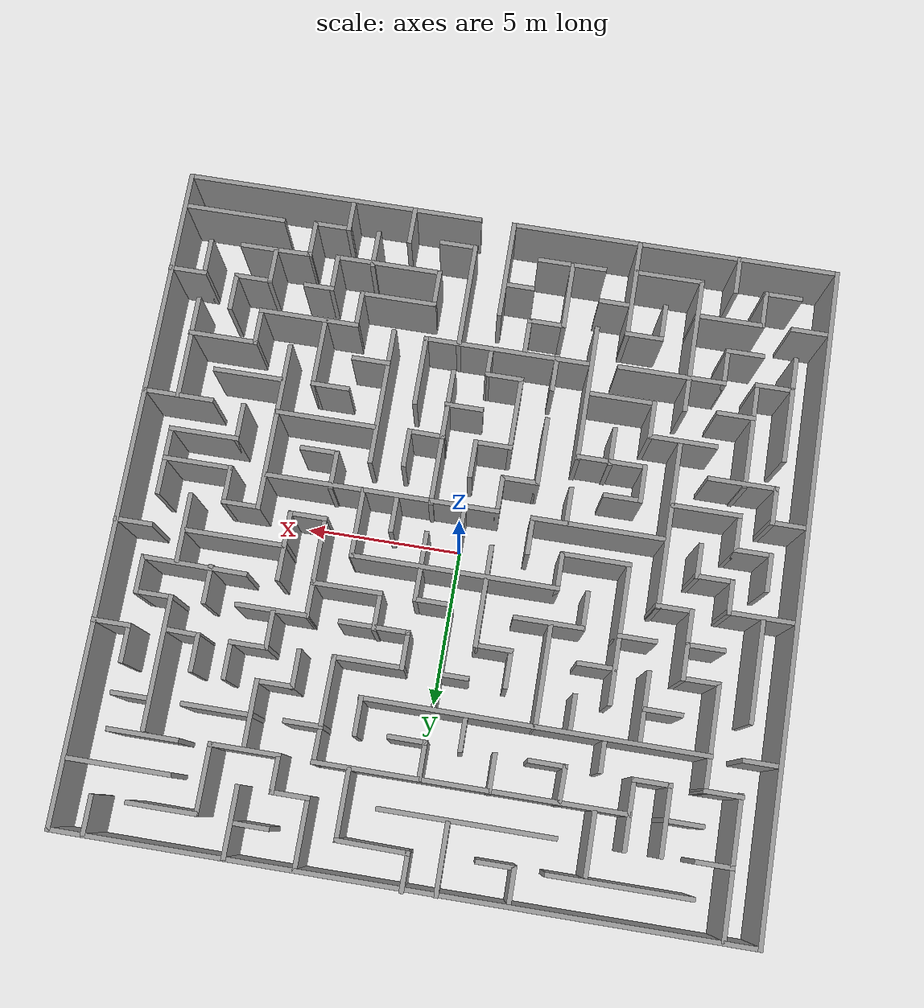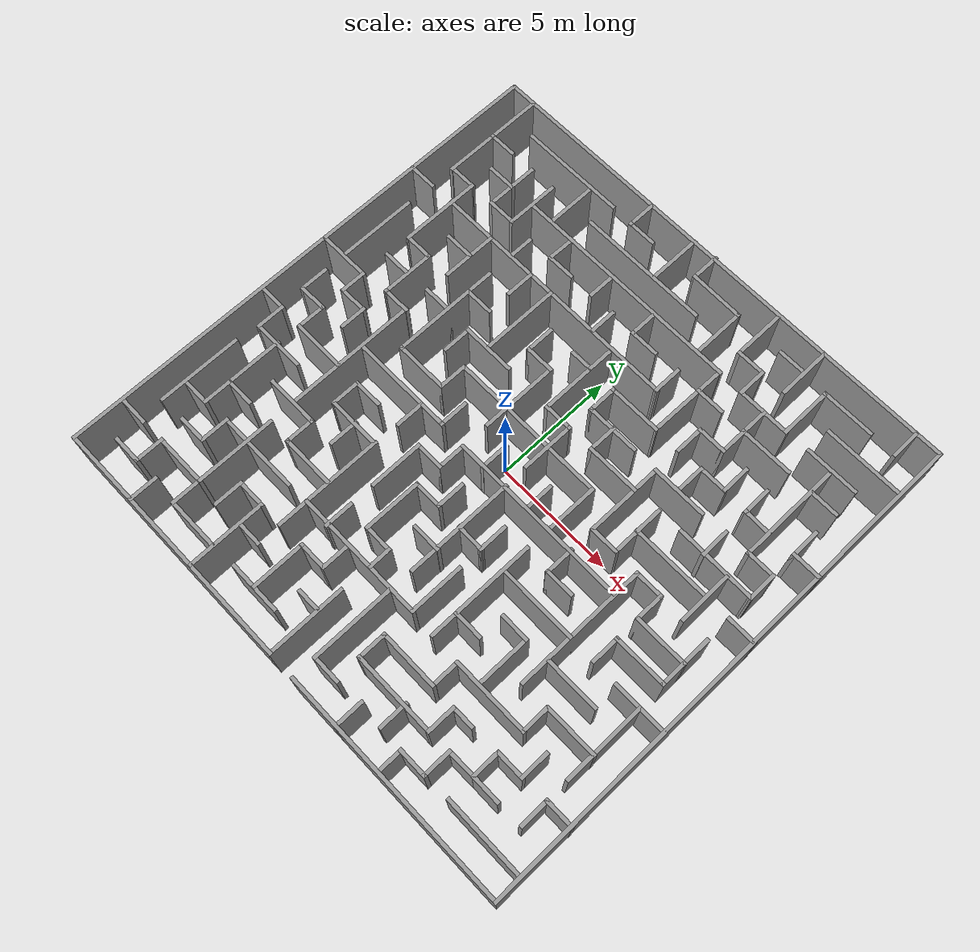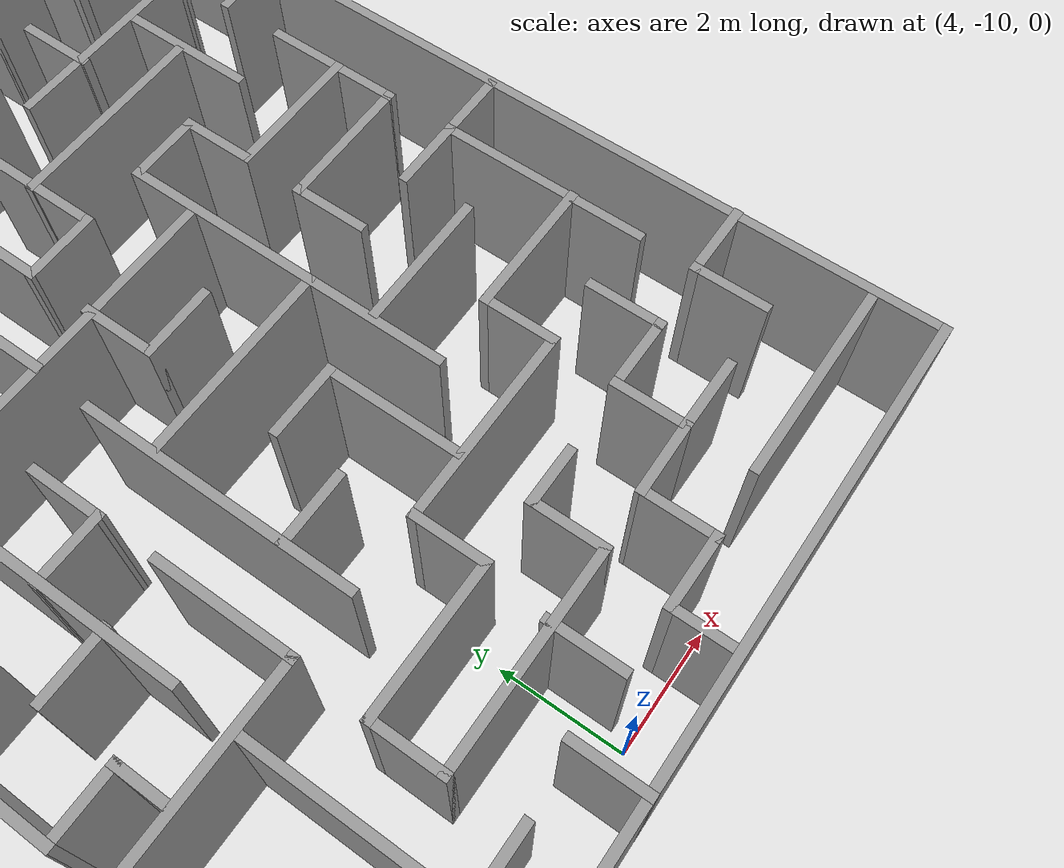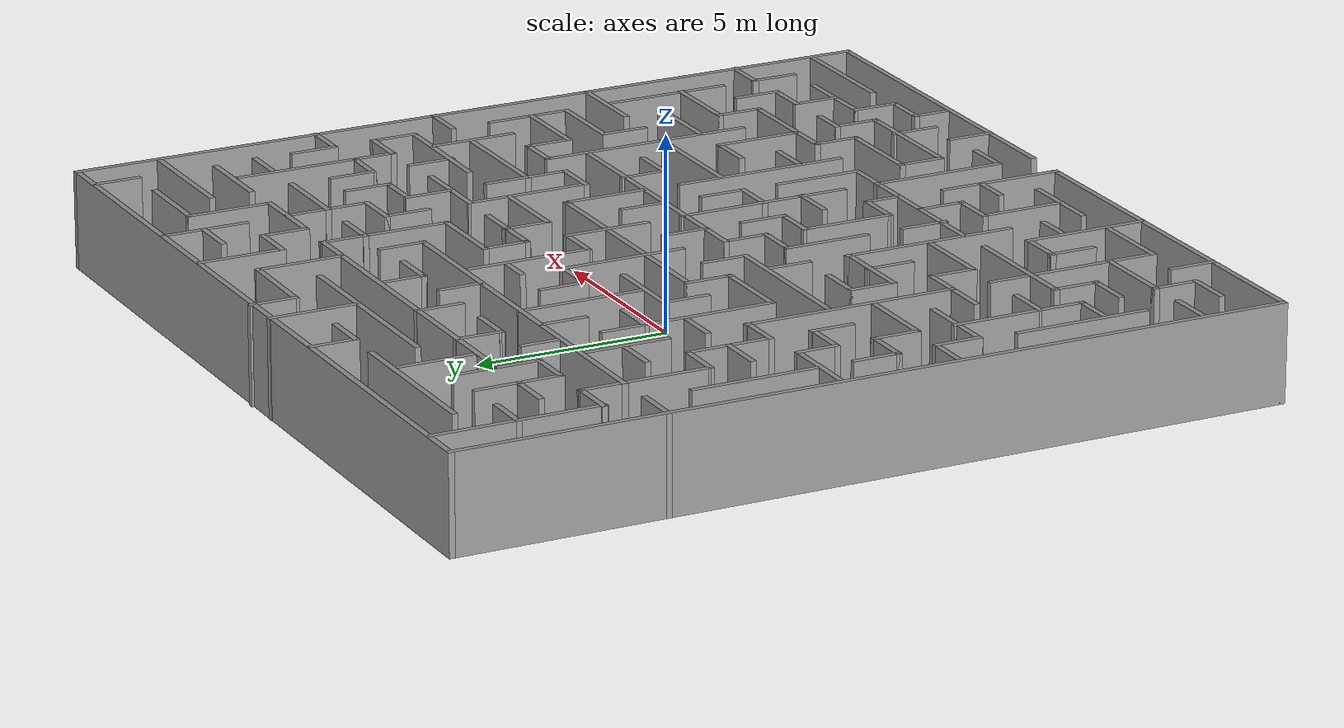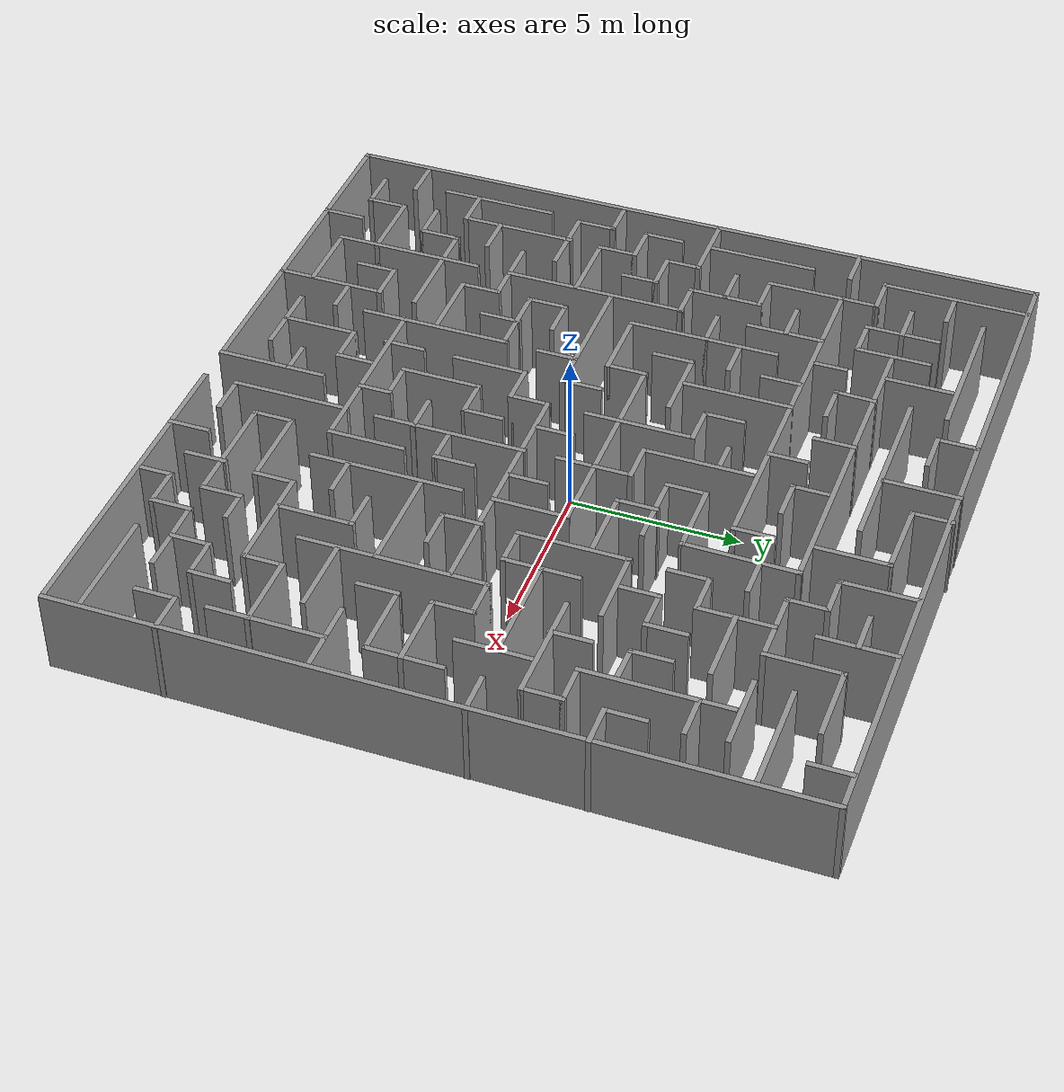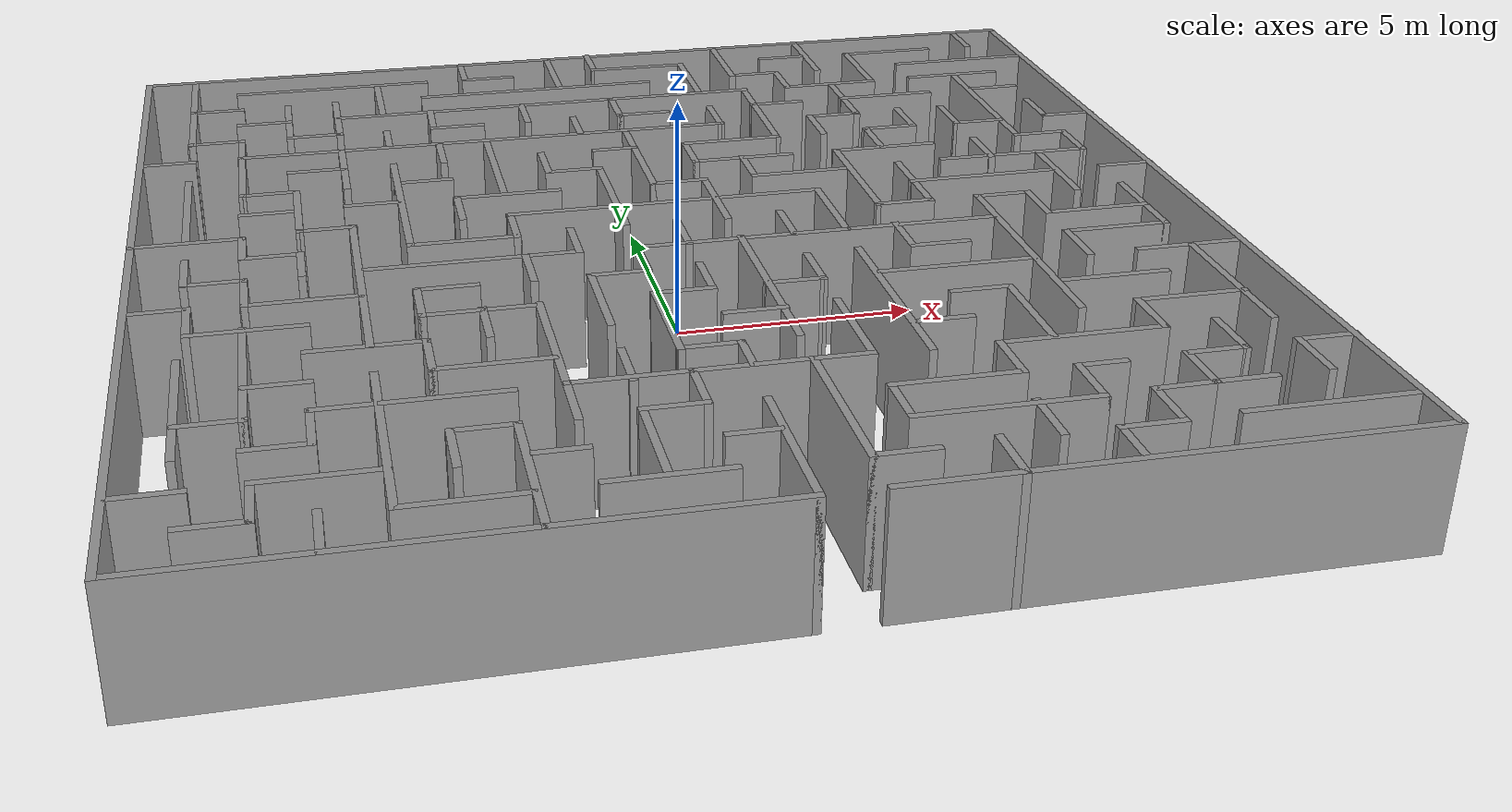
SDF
<?xml version='1.0'?>
<sdf version='1.7'>
  <model name='Maze_ej4'>
    <pose>-0.000546 0.061643 0 0 -0 0</pose>
    <link name='Wall_100'>
      <collision name='Wall_100_Collision'>
        <geometry>
          <box>
            <size>1.25 0.15 2.5</size>
          </box>
        </geometry>
        <pose>0 0 1.25 0 -0 0</pose>
      </collision>
      <visual name='Wall_100_Visual'>
        <pose>0 0 1.25 0 -0 0</pose>
        <geometry>
          <box>
            <size>1.25 0.15 2.5</size>
          </box>
        </geometry>
        <material>
          <script>
            <uri>file://media/materials/scripts/gazebo.material</uri>
            <name>Gazebo/Grey</name>
          </script>
          <ambient>1 1 1 1</ambient>
        </material>
        <meta>
          <layer>0</layer>
        </meta>
      </visual>
      <pose>-7.51415 -6.98122 0 0 -0 -1.5708</pose>
    </link>
    <link name='Wall_101'>
      <collision name='Wall_101_Collision'>
        <geometry>
          <box>
            <size>1.25 0.15 2.5</size>
          </box>
        </geometry>
        <pose>0 0 1.25 0 -0 0</pose>
      </collision>
      <visual name='Wall_101_Visual'>
        <pose>0 0 1.25 0 -0 0</pose>
        <geometry>
          <box>
            <size>1.25 0.15 2.5</size>
          </box>
        </geometry>
        <material>
          <script>
            <uri>file://media/materials/scripts/gazebo.material</uri>
            <name>Gazebo/Grey</name>
          </script>
          <ambient>1 1 1 1</ambient>
        </material>
        <meta>
          <layer>0</layer>
        </meta>
      </visual>
      <pose>-8.06415 -7.53122 0 0 -0 3.14159</pose>
    </link>
    <link name='Wall_103'>
      <collision name='Wall_103_Collision'>
        <geometry>
          <box>
            <size>1.25 0.15 2.5</size>
          </box>
        </geometry>
        <pose>0 0 1.25 0 -0 0</pose>
      </collision>
      <visual name='Wall_103_Visual'>
        <pose>0 0 1.25 0 -0 0</pose>
        <geometry>
          <box>
            <size>1.25 0.15 2.5</size>
          </box>
        </geometry>
        <material>
          <script>
            <uri>file://media/materials/scripts/gazebo.material</uri>
            <name>Gazebo/Grey</name>
          </script>
          <ambient>1 1 1 1</ambient>
        </material>
        <meta>
          <layer>0</layer>
        </meta>
      </visual>
      <pose>-1.63534 -7.51693 0 0 -0 0</pose>
    </link>
    <link name='Wall_104'>
      <collision name='Wall_104_Collision'>
        <geometry>
          <box>
            <size>1.25 0.15 2.5</size>
          </box>
        </geometry>
        <pose>0 0 1.25 0 -0 0</pose>
      </collision>
      <visual name='Wall_104_Visual'>
        <pose>0 0 1.25 0 -0 0</pose>
        <geometry>
          <box>
            <size>1.25 0.15 2.5</size>
          </box>
        </geometry>
        <material>
          <script>
            <uri>file://media/materials/scripts/gazebo.material</uri>
            <name>Gazebo/Grey</name>
          </script>
          <ambient>1 1 1 1</ambient>
        </material>
        <meta>
          <layer>0</layer>
        </meta>
      </visual>
      <pose>-1.08534 -6.96694 0 0 -0 1.5708</pose>
    </link>
    <link name='Wall_106'>
      <collision name='Wall_106_Collision'>
        <geometry>
          <box>
            <size>1 0.15 2.5</size>
          </box>
        </geometry>
        <pose>0 0 1.25 0 -0 0</pose>
      </collision>
      <visual name='Wall_106_Visual'>
        <pose>0 0 1.25 0 -0 0</pose>
        <geometry>
          <box>
            <size>1 0.15 2.5</size>
          </box>
        </geometry>
        <material>
          <script>
            <uri>file://media/materials/scripts/gazebo.material</uri>
            <name>Gazebo/Grey</name>
          </script>
          <ambient>1 1 1 1</ambient>
        </material>
        <meta>
          <layer>0</layer>
        </meta>
      </visual>
      <pose>-3.6867 -8.55744 0 0 -0 3.14159</pose>
    </link>
    <link name='Wall_116'>
      <collision name='Wall_116_Collision'>
        <geometry>
          <box>
            <size>2.25 0.15 2.5</size>
          </box>
        </geometry>
        <pose>0 0 1.25 0 -0 0</pose>
      </collision>
      <visual name='Wall_116_Visual'>
        <pose>0 0 1.25 0 -0 0</pose>
        <geometry>
          <box>
            <size>2.25 0.15 2.5</size>
          </box>
        </geometry>
        <material>
          <script>
            <uri>file://media/materials/scripts/gazebo.material</uri>
            <name>Gazebo/Grey</name>
          </script>
          <ambient>1 1 1 1</ambient>
        </material>
        <meta>
          <layer>0</layer>
        </meta>
      </visual>
      <pose>8.55467 -5.36811 0 0 -0 3.14159</pose>
    </link>
    <link name='Wall_117'>
      <collision name='Wall_117_Collision'>
        <geometry>
          <box>
            <size>1.25 0.15 2.5</size>
          </box>
        </geometry>
        <pose>0 0 1.25 0 -0 0</pose>
      </collision>
      <visual name='Wall_117_Visual'>
        <pose>0 0 1.25 0 -0 0</pose>
        <geometry>
          <box>
            <size>1.25 0.15 2.5</size>
          </box>
        </geometry>
        <material>
          <script>
            <uri>file://media/materials/scripts/gazebo.material</uri>
            <name>Gazebo/Grey</name>
          </script>
          <ambient>1 1 1 1</ambient>
        </material>
        <meta>
          <layer>0</layer>
        </meta>
      </visual>
      <pose>7.50467 -5.91811 0 0 -0 -1.5708</pose>
    </link>
    <link name='Wall_118'>
      <collision name='Wall_118_Collision'>
        <geometry>
          <box>
            <size>3.25 0.15 2.5</size>
          </box>
        </geometry>
        <pose>0 0 1.25 0 -0 0</pose>
      </collision>
      <visual name='Wall_118_Visual'>
        <pose>0 0 1.25 0 -0 0</pose>
        <geometry>
          <box>
            <size>3.25 0.15 2.5</size>
          </box>
        </geometry>
        <material>
          <script>
            <uri>file://media/materials/scripts/gazebo.material</uri>
            <name>Gazebo/Grey</name>
          </script>
          <ambient>1 1 1 1</ambient>
        </material>
        <meta>
          <layer>0</layer>
        </meta>
      </visual>
      <pose>5.95467 -6.46811 0 0 -0 3.14159</pose>
    </link>
    <link name='Wall_119'>
      <collision name='Wall_119_Collision'>
        <geometry>
          <box>
            <size>1.25 0.15 2.5</size>
          </box>
        </geometry>
        <pose>0 0 1.25 0 -0 0</pose>
      </collision>
      <visual name='Wall_119_Visual'>
        <pose>0 0 1.25 0 -0 0</pose>
        <geometry>
          <box>
            <size>1.25 0.15 2.5</size>
          </box>
        </geometry>
        <material>
          <script>
            <uri>file://media/materials/scripts/gazebo.material</uri>
            <name>Gazebo/Grey</name>
          </script>
          <ambient>1 1 1 1</ambient>
        </material>
        <meta>
          <layer>0</layer>
        </meta>
      </visual>
      <pose>4.40467 -7.01811 0 0 -0 -1.5708</pose>
    </link>
    <link name='Wall_120'>
      <collision name='Wall_120_Collision'>
        <geometry>
          <box>
            <size>2.5 0.15 2.5</size>
          </box>
        </geometry>
        <pose>0 0 1.25 0 -0 0</pose>
      </collision>
      <visual name='Wall_120_Visual'>
        <pose>0 0 1.25 0 -0 0</pose>
        <geometry>
          <box>
            <size>2.5 0.15 2.5</size>
          </box>
        </geometry>
        <material>
          <script>
            <uri>file://media/materials/scripts/gazebo.material</uri>
            <name>Gazebo/Grey</name>
          </script>
          <ambient>1 1 1 1</ambient>
        </material>
        <meta>
          <layer>0</layer>
        </meta>
      </visual>
      <pose>3.22967 -7.56811 0 0 -0 3.14159</pose>
    </link>
    <link name='Wall_121'>
      <collision name='Wall_121_Collision'>
        <geometry>
          <box>
            <size>1.25 0.15 2.5</size>
          </box>
        </geometry>
        <pose>0 0 1.25 0 -0 0</pose>
      </collision>
      <visual name='Wall_121_Visual'>
        <pose>0 0 1.25 0 -0 0</pose>
        <geometry>
          <box>
            <size>1.25 0.15 2.5</size>
          </box>
        </geometry>
        <material>
          <script>
            <uri>file://media/materials/scripts/gazebo.material</uri>
            <name>Gazebo/Grey</name>
          </script>
          <ambient>1 1 1 1</ambient>
        </material>
        <meta>
          <layer>0</layer>
        </meta>
      </visual>
      <pose>2.05467 -8.11811 0 0 -0 -1.5708</pose>
    </link>
    <link name='Wall_122'>
      <collision name='Wall_122_Collision'>
        <geometry>
          <box>
            <size>3.5 0.15 2.5</size>
          </box>
        </geometry>
        <pose>0 0 1.25 0 -0 0</pose>
      </collision>
      <visual name='Wall_122_Visual'>
        <pose>0 0 1.25 0 -0 0</pose>
        <geometry>
          <box>
            <size>3.5 0.15 2.5</size>
          </box>
        </geometry>
        <material>
          <script>
            <uri>file://media/materials/scripts/gazebo.material</uri>
            <name>Gazebo/Grey</name>
          </script>
          <ambient>1 1 1 1</ambient>
        </material>
        <meta>
          <layer>0</layer>
        </meta>
      </visual>
      <pose>3.72967 -8.66811 0 0 -0 0</pose>
    </link>
    <link name='Wall_123'>
      <collision name='Wall_123_Collision'>
        <geometry>
          <box>
            <size>1.25 0.15 2.5</size>
          </box>
        </geometry>
        <pose>0 0 1.25 0 -0 0</pose>
      </collision>
      <visual name='Wall_123_Visual'>
        <pose>0 0 1.25 0 -0 0</pose>
        <geometry>
          <box>
            <size>1.25 0.15 2.5</size>
          </box>
        </geometry>
        <material>
          <script>
            <uri>file://media/materials/scripts/gazebo.material</uri>
            <name>Gazebo/Grey</name>
          </script>
          <ambient>1 1 1 1</ambient>
        </material>
        <meta>
          <layer>0</layer>
        </meta>
      </visual>
      <pose>5.40467 -8.11811 0 0 -0 1.5708</pose>
    </link>
    <link name='Wall_124'>
      <collision name='Wall_124_Collision'>
        <geometry>
          <box>
            <size>1 0.15 2.5</size>
          </box>
        </geometry>
        <pose>0 0 1.25 0 -0 0</pose>
      </collision>
      <visual name='Wall_124_Visual'>
        <pose>0 0 1.25 0 -0 0</pose>
        <geometry>
          <box>
            <size>1 0.15 2.5</size>
          </box>
        </geometry>
        <material>
          <script>
            <uri>file://media/materials/scripts/gazebo.material</uri>
            <name>Gazebo/Grey</name>
          </script>
          <ambient>1 1 1 1</ambient>
        </material>
        <meta>
          <layer>0</layer>
        </meta>
      </visual>
      <pose>5.82967 -7.56811 0 0 -0 0</pose>
    </link>
    <link name='Wall_129'>
      <collision name='Wall_129_Collision'>
        <geometry>
          <box>
            <size>1.25 0.15 2.5</size>
          </box>
        </geometry>
        <pose>0 0 1.25 0 -0 0</pose>
      </collision>
      <visual name='Wall_129_Visual'>
        <pose>0 0 1.25 0 -0 0</pose>
        <geometry>
          <box>
            <size>1.25 0.15 2.5</size>
          </box>
        </geometry>
        <material>
          <script>
            <uri>file://media/materials/scripts/gazebo.material</uri>
            <name>Gazebo/Grey</name>
          </script>
          <ambient>1 1 1 1</ambient>
        </material>
        <meta>
          <layer>0</layer>
        </meta>
      </visual>
      <pose>3.20667 -10.1551 0 0 -0 1.5708</pose>
    </link>
    <link name='Wall_131'>
      <collision name='Wall_131_Collision'>
        <geometry>
          <box>
            <size>1.25 0.15 2.5</size>
          </box>
        </geometry>
        <pose>0 0 1.25 0 -0 0</pose>
      </collision>
      <visual name='Wall_131_Visual'>
        <pose>0 0 1.25 0 -0 0</pose>
        <geometry>
          <box>
            <size>1.25 0.15 2.5</size>
          </box>
        </geometry>
        <material>
          <script>
            <uri>file://media/materials/scripts/gazebo.material</uri>
            <name>Gazebo/Grey</name>
          </script>
          <ambient>1 1 1 1</ambient>
        </material>
        <meta>
          <layer>0</layer>
        </meta>
      </visual>
      <pose>8.53131 -6.96633 0 0 -0 -1.5708</pose>
    </link>
    <link name='Wall_132'>
      <collision name='Wall_132_Collision'>
        <geometry>
          <box>
            <size>1.25 0.15 2.5</size>
          </box>
        </geometry>
        <pose>0 0 1.25 0 -0 0</pose>
      </collision>
      <visual name='Wall_132_Visual'>
        <pose>0 0 1.25 0 -0 0</pose>
        <geometry>
          <box>
            <size>1.25 0.15 2.5</size>
          </box>
        </geometry>
        <material>
          <script>
            <uri>file://media/materials/scripts/gazebo.material</uri>
            <name>Gazebo/Grey</name>
          </script>
          <ambient>1 1 1 1</ambient>
        </material>
        <meta>
          <layer>0</layer>
        </meta>
      </visual>
      <pose>7.98132 -7.51633 0 0 -0 3.14159</pose>
    </link>
    <link name='Wall_133'>
      <collision name='Wall_133_Collision'>
        <geometry>
          <box>
            <size>1.23183 0.15 2.5</size>
          </box>
        </geometry>
        <pose>0 0 1.25 0 -0 0</pose>
      </collision>
      <visual name='Wall_133_Visual'>
        <pose>0 0 1.25 0 -0 0</pose>
        <geometry>
          <box>
            <size>1.23183 0.15 2.5</size>
          </box>
        </geometry>
        <material>
          <script>
            <uri>file://media/materials/scripts/gazebo.material</uri>
            <name>Gazebo/Grey</name>
          </script>
          <ambient>1 1 1 1</ambient>
        </material>
        <meta>
          <layer>0</layer>
        </meta>
      </visual>
      <pose>7.43131 -8.05724 0 0 -0 -1.5708</pose>
    </link>
    <link name='Wall_134'>
      <collision name='Wall_134_Collision'>
        <geometry>
          <box>
            <size>1.25015 0.15 2.5</size>
          </box>
        </geometry>
        <pose>0 0 1.25 0 -0 0</pose>
      </collision>
      <visual name='Wall_134_Visual'>
        <pose>0 0 1.25 0 -0 0</pose>
        <geometry>
          <box>
            <size>1.25015 0.15 2.5</size>
          </box>
        </geometry>
        <material>
          <script>
            <uri>file://media/materials/scripts/gazebo.material</uri>
            <name>Gazebo/Grey</name>
          </script>
          <ambient>1 1 1 1</ambient>
        </material>
        <meta>
          <layer>0</layer>
        </meta>
      </visual>
      <pose>6.88131 -8.60724 0 0 -0 -3.12507</pose>
    </link>
    <link name='Wall_135'>
      <collision name='Wall_135_Collision'>
        <geometry>
          <box>
            <size>1.25 0.15 2.5</size>
          </box>
        </geometry>
        <pose>0 0 1.25 0 -0 0</pose>
      </collision>
      <visual name='Wall_135_Visual'>
        <pose>0 0 1.25 0 -0 0</pose>
        <geometry>
          <box>
            <size>1.25 0.15 2.5</size>
          </box>
        </geometry>
        <material>
          <script>
            <uri>file://media/materials/scripts/gazebo.material</uri>
            <name>Gazebo/Grey</name>
          </script>
          <ambient>1 1 1 1</ambient>
        </material>
        <meta>
          <layer>0</layer>
        </meta>
      </visual>
      <pose>6.33132 -9.16633 0 0 -0 -1.5708</pose>
    </link>
    <link name='Wall_136'>
      <collision name='Wall_136_Collision'>
        <geometry>
          <box>
            <size>1.25 0.15 2.5</size>
          </box>
        </geometry>
        <pose>0 0 1.25 0 -0 0</pose>
      </collision>
      <visual name='Wall_136_Visual'>
        <pose>0 0 1.25 0 -0 0</pose>
        <geometry>
          <box>
            <size>1.25 0.15 2.5</size>
          </box>
        </geometry>
        <material>
          <script>
            <uri>file://media/materials/scripts/gazebo.material</uri>
            <name>Gazebo/Grey</name>
          </script>
          <ambient>1 1 1 1</ambient>
        </material>
        <meta>
          <layer>0</layer>
        </meta>
      </visual>
      <pose>5.78132 -9.71633 0 0 -0 3.14159</pose>
    </link>
    <link name='Wall_137'>
      <collision name='Wall_137_Collision'>
        <geometry>
          <box>
            <size>1 0.15 2.5</size>
          </box>
        </geometry>
        <pose>0 0 1.25 0 -0 0</pose>
      </collision>
      <visual name='Wall_137_Visual'>
        <pose>0 0 1.25 0 -0 0</pose>
        <geometry>
          <box>
            <size>1 0.15 2.5</size>
          </box>
        </geometry>
        <material>
          <script>
            <uri>file://media/materials/scripts/gazebo.material</uri>
            <name>Gazebo/Grey</name>
          </script>
          <ambient>1 1 1 1</ambient>
        </material>
        <meta>
          <layer>0</layer>
        </meta>
      </visual>
      <pose>5.23132 -10.1413 0 0 -0 -1.5708</pose>
    </link>
    <link name='Wall_14'>
      <collision name='Wall_14_Collision'>
        <geometry>
          <box>
            <size>9.75 0.15 2.5</size>
          </box>
        </geometry>
        <pose>0 0 1.25 0 -0 0</pose>
      </collision>
      <visual name='Wall_14_Visual'>
        <pose>0 0 1.25 0 -0 0</pose>
        <geometry>
          <box>
            <size>9.75 0.15 2.5</size>
          </box>
        </geometry>
        <material>
          <script>
            <uri>file://media/materials/scripts/gazebo.material</uri>
            <name>Gazebo/Grey</name>
          </script>
          <ambient>1 1 1 1</ambient>
        </material>
        <meta>
          <layer>0</layer>
        </meta>
      </visual>
      <pose>5.86667 -10.7039 0 0 -0 0</pose>
    </link>
    <link name='Wall_141'>
      <collision name='Wall_141_Collision'>
        <geometry>
          <box>
            <size>1.25 0.15 2.5</size>
          </box>
        </geometry>
        <pose>0 0 1.25 0 -0 0</pose>
      </collision>
      <visual name='Wall_141_Visual'>
        <pose>0 0 1.25 0 -0 0</pose>
        <geometry>
          <box>
            <size>1.25 0.15 2.5</size>
          </box>
        </geometry>
        <material>
          <script>
            <uri>file://media/materials/scripts/gazebo.material</uri>
            <name>Gazebo/Grey</name>
          </script>
          <ambient>1 1 1 1</ambient>
        </material>
        <meta>
          <layer>0</layer>
        </meta>
      </visual>
      <pose>7.98132 -8.59816 0 0 -0 0</pose>
    </link>
    <link name='Wall_143'>
      <collision name='Wall_143_Collision'>
        <geometry>
          <box>
            <size>3.25 0.15 2.5</size>
          </box>
        </geometry>
        <pose>0 0 1.25 0 -0 0</pose>
      </collision>
      <visual name='Wall_143_Visual'>
        <pose>0 0 1.25 0 -0 0</pose>
        <geometry>
          <box>
            <size>3.25 0.15 2.5</size>
          </box>
        </geometry>
        <material>
          <script>
            <uri>file://media/materials/scripts/gazebo.material</uri>
            <name>Gazebo/Grey</name>
          </script>
          <ambient>1 1 1 1</ambient>
        </material>
        <meta>
          <layer>0</layer>
        </meta>
      </visual>
      <pose>8.97277 -9.65109 0 0 -0 0</pose>
    </link>
    <link name='Wall_145'>
      <collision name='Wall_145_Collision'>
        <geometry>
          <box>
            <size>1.25 0.15 2.5</size>
          </box>
        </geometry>
        <pose>0 0 1.25 0 -0 0</pose>
      </collision>
      <visual name='Wall_145_Visual'>
        <pose>0 0 1.25 0 -0 0</pose>
        <geometry>
          <box>
            <size>1.25 0.15 2.5</size>
          </box>
        </geometry>
        <material>
          <script>
            <uri>file://media/materials/scripts/gazebo.material</uri>
            <name>Gazebo/Grey</name>
          </script>
          <ambient>1 1 1 1</ambient>
        </material>
        <meta>
          <layer>0</layer>
        </meta>
      </visual>
      <pose>9.58534 -7.99255 0 0 -0 1.5708</pose>
    </link>
    <link name='Wall_146'>
      <collision name='Wall_146_Collision'>
        <geometry>
          <box>
            <size>1.25 0.15 2.5</size>
          </box>
        </geometry>
        <pose>0 0 1.25 0 -0 0</pose>
      </collision>
      <visual name='Wall_146_Visual'>
        <pose>0 0 1.25 0 -0 0</pose>
        <geometry>
          <box>
            <size>1.25 0.15 2.5</size>
          </box>
        </geometry>
        <material>
          <script>
            <uri>file://media/materials/scripts/gazebo.material</uri>
            <name>Gazebo/Grey</name>
          </script>
          <ambient>1 1 1 1</ambient>
        </material>
        <meta>
          <layer>0</layer>
        </meta>
      </visual>
      <pose>10.1353 -7.44255 0 0 -0 0</pose>
    </link>
    <link name='Wall_148'>
      <collision name='Wall_148_Collision'>
        <geometry>
          <box>
            <size>3.42111 0.15 2.5</size>
          </box>
        </geometry>
        <pose>0 0 1.25 0 -0 0</pose>
      </collision>
      <visual name='Wall_148_Visual'>
        <pose>0 0 1.25 0 -0 0</pose>
        <geometry>
          <box>
            <size>3.42111 0.15 2.5</size>
          </box>
        </geometry>
        <material>
          <script>
            <uri>file://media/materials/scripts/gazebo.material</uri>
            <name>Gazebo/Grey</name>
          </script>
          <ambient>1 1 1 1</ambient>
        </material>
        <meta>
          <layer>0</layer>
        </meta>
      </visual>
      <pose>9.58534 -4.87164 0 0 -0 1.5708</pose>
    </link>
    <link name='Wall_15'>
      <collision name='Wall_15_Collision'>
        <geometry>
          <box>
            <size>21.5 0.15 2.5</size>
          </box>
        </geometry>
        <pose>0 0 1.25 0 -0 0</pose>
      </collision>
      <visual name='Wall_15_Visual'>
        <pose>0 0 1.25 0 -0 0</pose>
        <geometry>
          <box>
            <size>21.5 0.15 2.5</size>
          </box>
        </geometry>
        <material>
          <script>
            <uri>file://media/materials/scripts/gazebo.material</uri>
            <name>Gazebo/Grey</name>
          </script>
          <ambient>1 1 1 1</ambient>
        </material>
        <meta>
          <layer>0</layer>
        </meta>
      </visual>
      <pose>10.6667 -0.028895 0 0 -0 1.5708</pose>
    </link>
    <link name='Wall_150'>
      <collision name='Wall_150_Collision'>
        <geometry>
          <box>
            <size>2.25 0.15 2.5</size>
          </box>
        </geometry>
        <pose>0 0 1.25 0 -0 0</pose>
      </collision>
      <visual name='Wall_150_Visual'>
        <pose>0 0 1.25 0 -0 0</pose>
        <geometry>
          <box>
            <size>2.25 0.15 2.5</size>
          </box>
        </geometry>
        <material>
          <script>
            <uri>file://media/materials/scripts/gazebo.material</uri>
            <name>Gazebo/Grey</name>
          </script>
          <ambient>1 1 1 1</ambient>
        </material>
        <meta>
          <layer>0</layer>
        </meta>
      </visual>
      <pose>9.56314 -3.23608 0 0 -0 0</pose>
    </link>
    <link name='Wall_152'>
      <collision name='Wall_152_Collision'>
        <geometry>
          <box>
            <size>1.25 0.15 2.5</size>
          </box>
        </geometry>
        <pose>0 0 1.25 0 -0 0</pose>
      </collision>
      <visual name='Wall_152_Visual'>
        <pose>0 0 1.25 0 -0 0</pose>
        <geometry>
          <box>
            <size>1.25 0.15 2.5</size>
          </box>
        </geometry>
        <material>
          <script>
            <uri>file://media/materials/scripts/gazebo.material</uri>
            <name>Gazebo/Grey</name>
          </script>
          <ambient>1 1 1 1</ambient>
        </material>
        <meta>
          <layer>0</layer>
        </meta>
      </visual>
      <pose>4.86522 -4.30828 0 0 -0 0</pose>
    </link>
    <link name='Wall_153'>
      <collision name='Wall_153_Collision'>
        <geometry>
          <box>
            <size>2.25 0.15 2.5</size>
          </box>
        </geometry>
        <pose>0 0 1.25 0 -0 0</pose>
      </collision>
      <visual name='Wall_153_Visual'>
        <pose>0 0 1.25 0 -0 0</pose>
        <geometry>
          <box>
            <size>2.25 0.15 2.5</size>
          </box>
        </geometry>
        <material>
          <script>
            <uri>file://media/materials/scripts/gazebo.material</uri>
            <name>Gazebo/Grey</name>
          </script>
          <ambient>1 1 1 1</ambient>
        </material>
        <meta>
          <layer>0</layer>
        </meta>
      </visual>
      <pose>5.41522 -5.35828 0 0 -0 -1.5708</pose>
    </link>
    <link name='Wall_155'>
      <collision name='Wall_155_Collision'>
        <geometry>
          <box>
            <size>4.5 0.15 2.5</size>
          </box>
        </geometry>
        <pose>0 0 1.25 0 -0 0</pose>
      </collision>
      <visual name='Wall_155_Visual'>
        <pose>0 0 1.25 0 -0 0</pose>
        <geometry>
          <box>
            <size>4.5 0.15 2.5</size>
          </box>
        </geometry>
        <material>
          <script>
            <uri>file://media/materials/scripts/gazebo.material</uri>
            <name>Gazebo/Grey</name>
          </script>
          <ambient>1 1 1 1</ambient>
        </material>
        <meta>
          <layer>0</layer>
        </meta>
      </visual>
      <pose>3.17033 -4.2595 0 0 -0 1.5708</pose>
    </link>
    <link name='Wall_157'>
      <collision name='Wall_157_Collision'>
        <geometry>
          <box>
            <size>5.5 0.15 2.5</size>
          </box>
        </geometry>
        <pose>0 0 1.25 0 -0 0</pose>
      </collision>
      <visual name='Wall_157_Visual'>
        <pose>0 0 1.25 0 -0 0</pose>
        <geometry>
          <box>
            <size>5.5 0.15 2.5</size>
          </box>
        </geometry>
        <material>
          <script>
            <uri>file://media/materials/scripts/gazebo.material</uri>
            <name>Gazebo/Grey</name>
          </script>
          <ambient>1 1 1 1</ambient>
        </material>
        <meta>
          <layer>0</layer>
        </meta>
      </visual>
      <pose>6.36875 -2.72365 0 0 -0 1.5708</pose>
    </link>
    <link name='Wall_158'>
      <collision name='Wall_158_Collision'>
        <geometry>
          <box>
            <size>1.25 0.15 2.5</size>
          </box>
        </geometry>
        <pose>0 0 1.25 0 -0 0</pose>
      </collision>
      <visual name='Wall_158_Visual'>
        <pose>0 0 1.25 0 -0 0</pose>
        <geometry>
          <box>
            <size>1.25 0.15 2.5</size>
          </box>
        </geometry>
        <material>
          <script>
            <uri>file://media/materials/scripts/gazebo.material</uri>
            <name>Gazebo/Grey</name>
          </script>
          <ambient>1 1 1 1</ambient>
        </material>
        <meta>
          <layer>0</layer>
        </meta>
      </visual>
      <pose>6.91875 -0.048649 0 0 -0 0</pose>
    </link>
    <link name='Wall_159'>
      <collision name='Wall_159_Collision'>
        <geometry>
          <box>
            <size>1.25 0.15 2.5</size>
          </box>
        </geometry>
        <pose>0 0 1.25 0 -0 0</pose>
      </collision>
      <visual name='Wall_159_Visual'>
        <pose>0 0 1.25 0 -0 0</pose>
        <geometry>
          <box>
            <size>1.25 0.15 2.5</size>
          </box>
        </geometry>
        <material>
          <script>
            <uri>file://media/materials/scripts/gazebo.material</uri>
            <name>Gazebo/Grey</name>
          </script>
          <ambient>1 1 1 1</ambient>
        </material>
        <meta>
          <layer>0</layer>
        </meta>
      </visual>
      <pose>7.46875 -0.598649 0 0 -0 -1.5708</pose>
    </link>
    <link name='Wall_16'>
      <collision name='Wall_16_Collision'>
        <geometry>
          <box>
            <size>21.5 0.15 2.5</size>
          </box>
        </geometry>
        <pose>0 0 1.25 0 -0 0</pose>
      </collision>
      <visual name='Wall_16_Visual'>
        <pose>0 0 1.25 0 -0 0</pose>
        <geometry>
          <box>
            <size>21.5 0.15 2.5</size>
          </box>
        </geometry>
        <material>
          <script>
            <uri>file://media/materials/scripts/gazebo.material</uri>
            <name>Gazebo/Grey</name>
          </script>
          <ambient>1 1 1 1</ambient>
        </material>
        <meta>
          <layer>0</layer>
        </meta>
      </visual>
      <pose>-0.008328 10.6461 0 0 -0 3.14159</pose>
    </link>
    <link name='Wall_160'>
      <collision name='Wall_160_Collision'>
        <geometry>
          <box>
            <size>2.25 0.15 2.5</size>
          </box>
        </geometry>
        <pose>0 0 1.25 0 -0 0</pose>
      </collision>
      <visual name='Wall_160_Visual'>
        <pose>0 0 1.25 0 -0 0</pose>
        <geometry>
          <box>
            <size>2.25 0.15 2.5</size>
          </box>
        </geometry>
        <material>
          <script>
            <uri>file://media/materials/scripts/gazebo.material</uri>
            <name>Gazebo/Grey</name>
          </script>
          <ambient>1 1 1 1</ambient>
        </material>
        <meta>
          <layer>0</layer>
        </meta>
      </visual>
      <pose>8.51875 -1.14865 0 0 -0 0</pose>
    </link>
    <link name='Wall_162'>
      <collision name='Wall_162_Collision'>
        <geometry>
          <box>
            <size>2.25 0.15 2.5</size>
          </box>
        </geometry>
        <pose>0 0 1.25 0 -0 0</pose>
      </collision>
      <visual name='Wall_162_Visual'>
        <pose>0 0 1.25 0 -0 0</pose>
        <geometry>
          <box>
            <size>2.25 0.15 2.5</size>
          </box>
        </geometry>
        <material>
          <script>
            <uri>file://media/materials/scripts/gazebo.material</uri>
            <name>Gazebo/Grey</name>
          </script>
          <ambient>1 1 1 1</ambient>
        </material>
        <meta>
          <layer>0</layer>
        </meta>
      </visual>
      <pose>7.51766 -4.27193 0 0 -0 3.14159</pose>
    </link>
    <link name='Wall_164'>
      <collision name='Wall_164_Collision'>
        <geometry>
          <box>
            <size>3.25 0.15 2.5</size>
          </box>
        </geometry>
        <pose>0 0 1.25 0 -0 0</pose>
      </collision>
      <visual name='Wall_164_Visual'>
        <pose>0 0 1.25 0 -0 0</pose>
        <geometry>
          <box>
            <size>3.25 0.15 2.5</size>
          </box>
        </geometry>
        <material>
          <script>
            <uri>file://media/materials/scripts/gazebo.material</uri>
            <name>Gazebo/Grey</name>
          </script>
          <ambient>1 1 1 1</ambient>
        </material>
        <meta>
          <layer>0</layer>
        </meta>
      </visual>
      <pose>4.81875 -3.19974 0 0 -0 3.14159</pose>
    </link>
    <link name='Wall_166'>
      <collision name='Wall_166_Collision'>
        <geometry>
          <box>
            <size>1.25 0.15 2.5</size>
          </box>
        </geometry>
        <pose>0 0 1.25 0 -0 0</pose>
      </collision>
      <visual name='Wall_166_Visual'>
        <pose>0 0 1.25 0 -0 0</pose>
        <geometry>
          <box>
            <size>1.25 0.15 2.5</size>
          </box>
        </geometry>
        <material>
          <script>
            <uri>file://media/materials/scripts/gazebo.material</uri>
            <name>Gazebo/Grey</name>
          </script>
          <ambient>1 1 1 1</ambient>
        </material>
        <meta>
          <layer>0</layer>
        </meta>
      </visual>
      <pose>3.72887 -5.3623 0 0 -0 3.14159</pose>
    </link>
    <link name='Wall_168'>
      <collision name='Wall_168_Collision'>
        <geometry>
          <box>
            <size>1.25 0.15 2.5</size>
          </box>
        </geometry>
        <pose>0 0 1.25 0 -0 0</pose>
      </collision>
      <visual name='Wall_168_Visual'>
        <pose>0 0 1.25 0 -0 0</pose>
        <geometry>
          <box>
            <size>1.25 0.15 2.5</size>
          </box>
        </geometry>
        <material>
          <script>
            <uri>file://media/materials/scripts/gazebo.material</uri>
            <name>Gazebo/Grey</name>
          </script>
          <ambient>1 1 1 1</ambient>
        </material>
        <meta>
          <layer>0</layer>
        </meta>
      </visual>
      <pose>-0.00992 -2.67754 0 0 -0 -1.5708</pose>
    </link>
    <link name='Wall_17'>
      <collision name='Wall_17_Collision'>
        <geometry>
          <box>
            <size>21.5 0.15 2.5</size>
          </box>
        </geometry>
        <pose>0 0 1.25 0 -0 0</pose>
      </collision>
      <visual name='Wall_17_Visual'>
        <pose>0 0 1.25 0 -0 0</pose>
        <geometry>
          <box>
            <size>21.5 0.15 2.5</size>
          </box>
        </geometry>
        <material>
          <script>
            <uri>file://media/materials/scripts/gazebo.material</uri>
            <name>Gazebo/Grey</name>
          </script>
          <ambient>1 1 1 1</ambient>
        </material>
        <meta>
          <layer>0</layer>
        </meta>
      </visual>
      <pose>-10.6833 -0.028895 0 0 -0 -1.5708</pose>
    </link>
    <link name='Wall_171'>
      <collision name='Wall_171_Collision'>
        <geometry>
          <box>
            <size>1.25 0.15 2.5</size>
          </box>
        </geometry>
        <pose>0 0 1.25 0 -0 0</pose>
      </collision>
      <visual name='Wall_171_Visual'>
        <pose>0 0 1.25 0 -0 0</pose>
        <geometry>
          <box>
            <size>1.25 0.15 2.5</size>
          </box>
        </geometry>
        <material>
          <script>
            <uri>file://media/materials/scripts/gazebo.material</uri>
            <name>Gazebo/Grey</name>
          </script>
          <ambient>1 1 1 1</ambient>
        </material>
        <meta>
          <layer>0</layer>
        </meta>
      </visual>
      <pose>-0.55992 -3.22754 0 0 -0 3.14159</pose>
    </link>
    <link name='Wall_172'>
      <collision name='Wall_172_Collision'>
        <geometry>
          <box>
            <size>2.43059 0.15 2.5</size>
          </box>
        </geometry>
        <pose>0 0 1.25 0 -0 0</pose>
      </collision>
      <visual name='Wall_172_Visual'>
        <pose>0 0 1.25 0 -0 0</pose>
        <geometry>
          <box>
            <size>2.43059 0.15 2.5</size>
          </box>
        </geometry>
        <material>
          <script>
            <uri>file://media/materials/scripts/gazebo.material</uri>
            <name>Gazebo/Grey</name>
          </script>
          <ambient>1 1 1 1</ambient>
        </material>
        <meta>
          <layer>0</layer>
        </meta>
      </visual>
      <pose>-1.11419 -4.36761 0 0 -0 -1.57454</pose>
    </link>
    <link name='Wall_173'>
      <collision name='Wall_173_Collision'>
        <geometry>
          <box>
            <size>1.25 0.15 2.5</size>
          </box>
        </geometry>
        <pose>0 0 1.25 0 -0 0</pose>
      </collision>
      <visual name='Wall_173_Visual'>
        <pose>0 0 1.25 0 -0 0</pose>
        <geometry>
          <box>
            <size>1.25 0.15 2.5</size>
          </box>
        </geometry>
        <material>
          <script>
            <uri>file://media/materials/scripts/gazebo.material</uri>
            <name>Gazebo/Grey</name>
          </script>
          <ambient>1 1 1 1</ambient>
        </material>
        <meta>
          <layer>0</layer>
        </meta>
      </visual>
      <pose>-0.568463 -5.50769 0 0 -0 0</pose>
    </link>
    <link name='Wall_174'>
      <collision name='Wall_174_Collision'>
        <geometry>
          <box>
            <size>1 0.15 2.5</size>
          </box>
        </geometry>
        <pose>0 0 1.25 0 -0 0</pose>
      </collision>
      <visual name='Wall_174_Visual'>
        <pose>0 0 1.25 0 -0 0</pose>
        <geometry>
          <box>
            <size>1 0.15 2.5</size>
          </box>
        </geometry>
        <material>
          <script>
            <uri>file://media/materials/scripts/gazebo.material</uri>
            <name>Gazebo/Grey</name>
          </script>
          <ambient>1 1 1 1</ambient>
        </material>
        <meta>
          <layer>0</layer>
        </meta>
      </visual>
      <pose>-0.018463 -5.93269 0 0 -0 -1.5708</pose>
    </link>
    <link name='Wall_176'>
      <collision name='Wall_176_Collision'>
        <geometry>
          <box>
            <size>4.5 0.15 2.5</size>
          </box>
        </geometry>
        <pose>0 0 1.25 0 -0 0</pose>
      </collision>
      <visual name='Wall_176_Visual'>
        <pose>0 0 1.25 0 -0 0</pose>
        <geometry>
          <box>
            <size>4.5 0.15 2.5</size>
          </box>
        </geometry>
        <material>
          <script>
            <uri>file://media/materials/scripts/gazebo.material</uri>
            <name>Gazebo/Grey</name>
          </script>
          <ambient>1 1 1 1</ambient>
        </material>
        <meta>
          <layer>0</layer>
        </meta>
      </visual>
      <pose>1.06228 -3.24182 0 0 -0 1.5708</pose>
    </link>
    <link name='Wall_178'>
      <collision name='Wall_178_Collision'>
        <geometry>
          <box>
            <size>1.25 0.15 2.5</size>
          </box>
        </geometry>
        <pose>0 0 1.25 0 -0 0</pose>
      </collision>
      <visual name='Wall_178_Visual'>
        <pose>0 0 1.25 0 -0 0</pose>
        <geometry>
          <box>
            <size>1.25 0.15 2.5</size>
          </box>
        </geometry>
        <material>
          <script>
            <uri>file://media/materials/scripts/gazebo.material</uri>
            <name>Gazebo/Grey</name>
          </script>
          <ambient>1 1 1 1</ambient>
        </material>
        <meta>
          <layer>0</layer>
        </meta>
      </visual>
      <pose>2.1163 -2.69571 0 0 -0 -1.5708</pose>
    </link>
    <link name='Wall_179'>
      <collision name='Wall_179_Collision'>
        <geometry>
          <box>
            <size>1.22224 0.15 2.5</size>
          </box>
        </geometry>
        <pose>0 0 1.25 0 -0 0</pose>
      </collision>
      <visual name='Wall_179_Visual'>
        <pose>0 0 1.25 0 -0 0</pose>
        <geometry>
          <box>
            <size>1.22224 0.15 2.5</size>
          </box>
        </geometry>
        <material>
          <script>
            <uri>file://media/materials/scripts/gazebo.material</uri>
            <name>Gazebo/Grey</name>
          </script>
          <ambient>1 1 1 1</ambient>
        </material>
        <meta>
          <layer>0</layer>
        </meta>
      </visual>
      <pose>1.5802 -3.2409 0 0 -0 3.13261</pose>
    </link>
    <link name='Wall_18'>
      <collision name='Wall_18_Collision'>
        <geometry>
          <box>
            <size>10.75 0.15 2.5</size>
          </box>
        </geometry>
        <pose>0 0 1.25 0 -0 0</pose>
      </collision>
      <visual name='Wall_18_Visual'>
        <pose>0 0 1.25 0 -0 0</pose>
        <geometry>
          <box>
            <size>10.75 0.15 2.5</size>
          </box>
        </geometry>
        <material>
          <script>
            <uri>file://media/materials/scripts/gazebo.material</uri>
            <name>Gazebo/Grey</name>
          </script>
          <ambient>1 1 1 1</ambient>
        </material>
        <meta>
          <layer>0</layer>
        </meta>
      </visual>
      <pose>-5.38333 -10.7039 0 0 -0 0</pose>
    </link>
    <link name='Wall_181'>
      <collision name='Wall_181_Collision'>
        <geometry>
          <box>
            <size>1.25 0.15 2.5</size>
          </box>
        </geometry>
        <pose>0 0 1.25 0 -0 0</pose>
      </collision>
      <visual name='Wall_181_Visual'>
        <pose>0 0 1.25 0 -0 0</pose>
        <geometry>
          <box>
            <size>1.25 0.15 2.5</size>
          </box>
        </geometry>
        <material>
          <script>
            <uri>file://media/materials/scripts/gazebo.material</uri>
            <name>Gazebo/Grey</name>
          </script>
          <ambient>1 1 1 1</ambient>
        </material>
        <meta>
          <layer>0</layer>
        </meta>
      </visual>
      <pose>0.54008 -4.30828 0 0 -0 0</pose>
    </link>
    <link name='Wall_183'>
      <collision name='Wall_183_Collision'>
        <geometry>
          <box>
            <size>1.25 0.15 2.5</size>
          </box>
        </geometry>
        <pose>0 0 1.25 0 -0 0</pose>
      </collision>
      <visual name='Wall_183_Visual'>
        <pose>0 0 1.25 0 -0 0</pose>
        <geometry>
          <box>
            <size>1.25 0.15 2.5</size>
          </box>
        </geometry>
        <material>
          <script>
            <uri>file://media/materials/scripts/gazebo.material</uri>
            <name>Gazebo/Grey</name>
          </script>
          <ambient>1 1 1 1</ambient>
        </material>
        <meta>
          <layer>0</layer>
        </meta>
      </visual>
      <pose>-2.13614 -5.9123 0 0 -0 -1.5708</pose>
    </link>
    <link name='Wall_185'>
      <collision name='Wall_185_Collision'>
        <geometry>
          <box>
            <size>1.25 0.15 2.5</size>
          </box>
        </geometry>
        <pose>0 0 1.25 0 -0 0</pose>
      </collision>
      <visual name='Wall_185_Visual'>
        <pose>0 0 1.25 0 -0 0</pose>
        <geometry>
          <box>
            <size>1.25 0.15 2.5</size>
          </box>
        </geometry>
        <material>
          <script>
            <uri>file://media/materials/scripts/gazebo.material</uri>
            <name>Gazebo/Grey</name>
          </script>
          <ambient>1 1 1 1</ambient>
        </material>
        <meta>
          <layer>0</layer>
        </meta>
      </visual>
      <pose>-4.84871 -2.18206 0 0 -0 3.14159</pose>
    </link>
    <link name='Wall_186'>
      <collision name='Wall_186_Collision'>
        <geometry>
          <box>
            <size>1.25 0.15 2.5</size>
          </box>
        </geometry>
        <pose>0 0 1.25 0 -0 0</pose>
      </collision>
      <visual name='Wall_186_Visual'>
        <pose>0 0 1.25 0 -0 0</pose>
        <geometry>
          <box>
            <size>1.25 0.15 2.5</size>
          </box>
        </geometry>
        <material>
          <script>
            <uri>file://media/materials/scripts/gazebo.material</uri>
            <name>Gazebo/Grey</name>
          </script>
          <ambient>1 1 1 1</ambient>
        </material>
        <meta>
          <layer>0</layer>
        </meta>
      </visual>
      <pose>-5.39871 -2.73206 0 0 -0 -1.5708</pose>
    </link>
    <link name='Wall_187'>
      <collision name='Wall_187_Collision'>
        <geometry>
          <box>
            <size>2.25 0.15 2.5</size>
          </box>
        </geometry>
        <pose>0 0 1.25 0 -0 0</pose>
      </collision>
      <visual name='Wall_187_Visual'>
        <pose>0 0 1.25 0 -0 0</pose>
        <geometry>
          <box>
            <size>2.25 0.15 2.5</size>
          </box>
        </geometry>
        <material>
          <script>
            <uri>file://media/materials/scripts/gazebo.material</uri>
            <name>Gazebo/Grey</name>
          </script>
          <ambient>1 1 1 1</ambient>
        </material>
        <meta>
          <layer>0</layer>
        </meta>
      </visual>
      <pose>-4.34871 -3.28206 0 0 -0 0</pose>
    </link>
    <link name='Wall_189'>
      <collision name='Wall_189_Collision'>
        <geometry>
          <box>
            <size>1.25 0.15 2.5</size>
          </box>
        </geometry>
        <pose>0 0 1.25 0 -0 0</pose>
      </collision>
      <visual name='Wall_189_Visual'>
        <pose>0 0 1.25 0 -0 0</pose>
        <geometry>
          <box>
            <size>1.25 0.15 2.5</size>
          </box>
        </geometry>
        <material>
          <script>
            <uri>file://media/materials/scripts/gazebo.material</uri>
            <name>Gazebo/Grey</name>
          </script>
          <ambient>1 1 1 1</ambient>
        </material>
        <meta>
          <layer>0</layer>
        </meta>
      </visual>
      <pose>-4.29871 -3.78608 0 0 -0 -1.5708</pose>
    </link>
    <link name='Wall_19'>
      <collision name='Wall_19_Collision'>
        <geometry>
          <box>
            <size>3.25 0.15 2.5</size>
          </box>
        </geometry>
        <pose>0 0 1.25 0 -0 0</pose>
      </collision>
      <visual name='Wall_19_Visual'>
        <pose>0 0 1.25 0 -0 0</pose>
        <geometry>
          <box>
            <size>3.25 0.15 2.5</size>
          </box>
        </geometry>
        <material>
          <script>
            <uri>file://media/materials/scripts/gazebo.material</uri>
            <name>Gazebo/Grey</name>
          </script>
          <ambient>1 1 1 1</ambient>
        </material>
        <meta>
          <layer>0</layer>
        </meta>
      </visual>
      <pose>-0.083328 -9.1539 0 0 -0 1.5708</pose>
    </link>
    <link name='Wall_191'>
      <collision name='Wall_191_Collision'>
        <geometry>
          <box>
            <size>2.25 0.15 2.5</size>
          </box>
        </geometry>
        <pose>0 0 1.25 0 -0 0</pose>
      </collision>
      <visual name='Wall_191_Visual'>
        <pose>0 0 1.25 0 -0 0</pose>
        <geometry>
          <box>
            <size>2.25 0.15 2.5</size>
          </box>
        </geometry>
        <material>
          <script>
            <uri>file://media/materials/scripts/gazebo.material</uri>
            <name>Gazebo/Grey</name>
          </script>
          <ambient>1 1 1 1</ambient>
        </material>
        <meta>
          <layer>0</layer>
        </meta>
      </visual>
      <pose>-2.1319 -3.27188 0 0 -0 1.5708</pose>
    </link>
    <link name='Wall_192'>
      <collision name='Wall_192_Collision'>
        <geometry>
          <box>
            <size>1.25 0.15 2.5</size>
          </box>
        </geometry>
        <pose>0 0 1.25 0 -0 0</pose>
      </collision>
      <visual name='Wall_192_Visual'>
        <pose>0 0 1.25 0 -0 0</pose>
        <geometry>
          <box>
            <size>1.25 0.15 2.5</size>
          </box>
        </geometry>
        <material>
          <script>
            <uri>file://media/materials/scripts/gazebo.material</uri>
            <name>Gazebo/Grey</name>
          </script>
          <ambient>1 1 1 1</ambient>
        </material>
        <meta>
          <layer>0</layer>
        </meta>
      </visual>
      <pose>-1.5819 -2.22188 0 0 -0 0</pose>
    </link>
    <link name='Wall_193'>
      <collision name='Wall_193_Collision'>
        <geometry>
          <box>
            <size>1.25 0.15 2.5</size>
          </box>
        </geometry>
        <pose>0 0 1.25 0 -0 0</pose>
      </collision>
      <visual name='Wall_193_Visual'>
        <pose>0 0 1.25 0 -0 0</pose>
        <geometry>
          <box>
            <size>1.25 0.15 2.5</size>
          </box>
        </geometry>
        <material>
          <script>
            <uri>file://media/materials/scripts/gazebo.material</uri>
            <name>Gazebo/Grey</name>
          </script>
          <ambient>1 1 1 1</ambient>
        </material>
        <meta>
          <layer>0</layer>
        </meta>
      </visual>
      <pose>-1.0319 -1.67188 0 0 -0 1.5708</pose>
    </link>
    <link name='Wall_194'>
      <collision name='Wall_194_Collision'>
        <geometry>
          <box>
            <size>7.5 0.15 2.5</size>
          </box>
        </geometry>
        <pose>0 0 1.25 0 -0 0</pose>
      </collision>
      <visual name='Wall_194_Visual'>
        <pose>0 0 1.25 0 -0 0</pose>
        <geometry>
          <box>
            <size>7.5 0.15 2.5</size>
          </box>
        </geometry>
        <material>
          <script>
            <uri>file://media/materials/scripts/gazebo.material</uri>
            <name>Gazebo/Grey</name>
          </script>
          <ambient>1 1 1 1</ambient>
        </material>
        <meta>
          <layer>0</layer>
        </meta>
      </visual>
      <pose>2.6431 -1.12188 0 0 -0 0</pose>
    </link>
    <link name='Wall_196'>
      <collision name='Wall_196_Collision'>
        <geometry>
          <box>
            <size>1.25 0.15 2.5</size>
          </box>
        </geometry>
        <pose>0 0 1.25 0 -0 0</pose>
      </collision>
      <visual name='Wall_196_Visual'>
        <pose>0 0 1.25 0 -0 0</pose>
        <geometry>
          <box>
            <size>1.25 0.15 2.5</size>
          </box>
        </geometry>
        <material>
          <script>
            <uri>file://media/materials/scripts/gazebo.material</uri>
            <name>Gazebo/Grey</name>
          </script>
          <ambient>1 1 1 1</ambient>
        </material>
        <meta>
          <layer>0</layer>
        </meta>
      </visual>
      <pose>4.25677 -1.61398 0 0 -0 -1.5708</pose>
    </link>
    <link name='Wall_197'>
      <collision name='Wall_197_Collision'>
        <geometry>
          <box>
            <size>1.25 0.15 2.5</size>
          </box>
        </geometry>
        <pose>0 0 1.25 0 -0 0</pose>
      </collision>
      <visual name='Wall_197_Visual'>
        <pose>0 0 1.25 0 -0 0</pose>
        <geometry>
          <box>
            <size>1.25 0.15 2.5</size>
          </box>
        </geometry>
        <material>
          <script>
            <uri>file://media/materials/scripts/gazebo.material</uri>
            <name>Gazebo/Grey</name>
          </script>
          <ambient>1 1 1 1</ambient>
        </material>
        <meta>
          <layer>0</layer>
        </meta>
      </visual>
      <pose>4.80677 -2.16398 0 0 -0 0</pose>
    </link>
    <link name='Wall_199'>
      <collision name='Wall_199_Collision'>
        <geometry>
          <box>
            <size>1.25 0.15 2.5</size>
          </box>
        </geometry>
        <pose>0 0 1.25 0 -0 0</pose>
      </collision>
      <visual name='Wall_199_Visual'>
        <pose>0 0 1.25 0 -0 0</pose>
        <geometry>
          <box>
            <size>1.25 0.15 2.5</size>
          </box>
        </geometry>
        <material>
          <script>
            <uri>file://media/materials/scripts/gazebo.material</uri>
            <name>Gazebo/Grey</name>
          </script>
          <ambient>1 1 1 1</ambient>
        </material>
        <meta>
          <layer>0</layer>
        </meta>
      </visual>
      <pose>7.467 -2.67532 0 0 -0 1.5708</pose>
    </link>
    <link name='Wall_200'>
      <collision name='Wall_200_Collision'>
        <geometry>
          <box>
            <size>2.25 0.15 2.5</size>
          </box>
        </geometry>
        <pose>0 0 1.25 0 -0 0</pose>
      </collision>
      <visual name='Wall_200_Visual'>
        <pose>0 0 1.25 0 -0 0</pose>
        <geometry>
          <box>
            <size>2.25 0.15 2.5</size>
          </box>
        </geometry>
        <material>
          <script>
            <uri>file://media/materials/scripts/gazebo.material</uri>
            <name>Gazebo/Grey</name>
          </script>
          <ambient>1 1 1 1</ambient>
        </material>
        <meta>
          <layer>0</layer>
        </meta>
      </visual>
      <pose>8.517 -2.12532 0 0 -0 0</pose>
    </link>
    <link name='Wall_201'>
      <collision name='Wall_201_Collision'>
        <geometry>
          <box>
            <size>2.25 0.15 2.5</size>
          </box>
        </geometry>
        <pose>0 0 1.25 0 -0 0</pose>
      </collision>
      <visual name='Wall_201_Visual'>
        <pose>0 0 1.25 0 -0 0</pose>
        <geometry>
          <box>
            <size>2.25 0.15 2.5</size>
          </box>
        </geometry>
        <material>
          <script>
            <uri>file://media/materials/scripts/gazebo.material</uri>
            <name>Gazebo/Grey</name>
          </script>
          <ambient>1 1 1 1</ambient>
        </material>
        <meta>
          <layer>0</layer>
        </meta>
      </visual>
      <pose>9.567 -1.07532 0 0 -0 1.5708</pose>
    </link>
    <link name='Wall_205'>
      <collision name='Wall_205_Collision'>
        <geometry>
          <box>
            <size>1.25 0.15 2.5</size>
          </box>
        </geometry>
        <pose>0 0 1.25 0 -0 0</pose>
      </collision>
      <visual name='Wall_205_Visual'>
        <pose>0 0 1.25 0 -0 0</pose>
        <geometry>
          <box>
            <size>1.25 0.15 2.5</size>
          </box>
        </geometry>
        <material>
          <script>
            <uri>file://media/materials/scripts/gazebo.material</uri>
            <name>Gazebo/Grey</name>
          </script>
          <ambient>1 1 1 1</ambient>
        </material>
        <meta>
          <layer>0</layer>
        </meta>
      </visual>
      <pose>-2.16368 -0.533309 0 0 -0 -1.5708</pose>
    </link>
    <link name='Wall_206'>
      <collision name='Wall_206_Collision'>
        <geometry>
          <box>
            <size>4.25 0.15 2.5</size>
          </box>
        </geometry>
        <pose>0 0 1.25 0 -0 0</pose>
      </collision>
      <visual name='Wall_206_Visual'>
        <pose>0 0 1.25 0 -0 0</pose>
        <geometry>
          <box>
            <size>4.25 0.15 2.5</size>
          </box>
        </geometry>
        <material>
          <script>
            <uri>file://media/materials/scripts/gazebo.material</uri>
            <name>Gazebo/Grey</name>
          </script>
          <ambient>1 1 1 1</ambient>
        </material>
        <meta>
          <layer>0</layer>
        </meta>
      </visual>
      <pose>-4.21368 -1.08331 0 0 -0 3.14159</pose>
    </link>
    <link name='Wall_208'>
      <collision name='Wall_208_Collision'>
        <geometry>
          <box>
            <size>1.25 0.15 2.5</size>
          </box>
        </geometry>
        <pose>0 0 1.25 0 -0 0</pose>
      </collision>
      <visual name='Wall_208_Visual'>
        <pose>0 0 1.25 0 -0 0</pose>
        <geometry>
          <box>
            <size>1.25 0.15 2.5</size>
          </box>
        </geometry>
        <material>
          <script>
            <uri>file://media/materials/scripts/gazebo.material</uri>
            <name>Gazebo/Grey</name>
          </script>
          <ambient>1 1 1 1</ambient>
        </material>
        <meta>
          <layer>0</layer>
        </meta>
      </visual>
      <pose>-3.21257 -1.64233 0 0 -0 1.5708</pose>
    </link>
    <link name='Wall_21'>
      <collision name='Wall_21_Collision'>
        <geometry>
          <box>
            <size>1 0.15 2.5</size>
          </box>
        </geometry>
        <pose>0 0 1.25 0 -0 0</pose>
      </collision>
      <visual name='Wall_21_Visual'>
        <pose>0 0 1.25 0 -0 0</pose>
        <geometry>
          <box>
            <size>1 0.15 2.5</size>
          </box>
        </geometry>
        <material>
          <script>
            <uri>file://media/materials/scripts/gazebo.material</uri>
            <name>Gazebo/Grey</name>
          </script>
          <ambient>1 1 1 1</ambient>
        </material>
        <meta>
          <layer>0</layer>
        </meta>
      </visual>
      <pose>-0.574567 -8.62093 0 0 -0 0</pose>
    </link>
    <link name='Wall_212'>
      <collision name='Wall_212_Collision'>
        <geometry>
          <box>
            <size>4.5 0.15 2.5</size>
          </box>
        </geometry>
        <pose>0 0 1.25 0 -0 0</pose>
      </collision>
      <visual name='Wall_212_Visual'>
        <pose>0 0 1.25 0 -0 0</pose>
        <geometry>
          <box>
            <size>4.5 0.15 2.5</size>
          </box>
        </geometry>
        <material>
          <script>
            <uri>file://media/materials/scripts/gazebo.material</uri>
            <name>Gazebo/Grey</name>
          </script>
          <ambient>1 1 1 1</ambient>
        </material>
        <meta>
          <layer>0</layer>
        </meta>
      </visual>
      <pose>-5.34212 2.06902 0 0 -0 -1.5708</pose>
    </link>
    <link name='Wall_213'>
      <collision name='Wall_213_Collision'>
        <geometry>
          <box>
            <size>2.25 0.15 2.5</size>
          </box>
        </geometry>
        <pose>0 0 1.25 0 -0 0</pose>
      </collision>
      <visual name='Wall_213_Visual'>
        <pose>0 0 1.25 0 -0 0</pose>
        <geometry>
          <box>
            <size>2.25 0.15 2.5</size>
          </box>
        </geometry>
        <material>
          <script>
            <uri>file://media/materials/scripts/gazebo.material</uri>
            <name>Gazebo/Grey</name>
          </script>
          <ambient>1 1 1 1</ambient>
        </material>
        <meta>
          <layer>0</layer>
        </meta>
      </visual>
      <pose>-4.29212 -0.105982 0 0 -0 0</pose>
    </link>
    <link name='Wall_214'>
      <collision name='Wall_214_Collision'>
        <geometry>
          <box>
            <size>1.25 0.15 2.5</size>
          </box>
        </geometry>
        <pose>0 0 1.25 0 -0 0</pose>
      </collision>
      <visual name='Wall_214_Visual'>
        <pose>0 0 1.25 0 -0 0</pose>
        <geometry>
          <box>
            <size>1.25 0.15 2.5</size>
          </box>
        </geometry>
        <material>
          <script>
            <uri>file://media/materials/scripts/gazebo.material</uri>
            <name>Gazebo/Grey</name>
          </script>
          <ambient>1 1 1 1</ambient>
        </material>
        <meta>
          <layer>0</layer>
        </meta>
      </visual>
      <pose>-3.24212 0.444018 0 0 -0 1.5708</pose>
    </link>
    <link name='Wall_215'>
      <collision name='Wall_215_Collision'>
        <geometry>
          <box>
            <size>6.57519 0.15 2.5</size>
          </box>
        </geometry>
        <pose>0 0 1.25 0 -0 0</pose>
      </collision>
      <visual name='Wall_215_Visual'>
        <pose>0 0 1.25 0 -0 0</pose>
        <geometry>
          <box>
            <size>6.57519 0.15 2.5</size>
          </box>
        </geometry>
        <material>
          <script>
            <uri>file://media/materials/scripts/gazebo.material</uri>
            <name>Gazebo/Grey</name>
          </script>
          <ambient>1 1 1 1</ambient>
        </material>
        <meta>
          <layer>0</layer>
        </meta>
      </visual>
      <pose>-0.029528 0.994018 0 0 -0 0</pose>
    </link>
    <link name='Wall_216'>
      <collision name='Wall_216_Collision'>
        <geometry>
          <box>
            <size>2.25 0.15 2.5</size>
          </box>
        </geometry>
        <pose>0 0 1.25 0 -0 0</pose>
      </collision>
      <visual name='Wall_216_Visual'>
        <pose>0 0 1.25 0 -0 0</pose>
        <geometry>
          <box>
            <size>2.25 0.15 2.5</size>
          </box>
        </geometry>
        <material>
          <script>
            <uri>file://media/materials/scripts/gazebo.material</uri>
            <name>Gazebo/Grey</name>
          </script>
          <ambient>1 1 1 1</ambient>
        </material>
        <meta>
          <layer>0</layer>
        </meta>
      </visual>
      <pose>3.21485 -0.055982 0 0 -0 -1.5708</pose>
    </link>
    <link name='Wall_218'>
      <collision name='Wall_218_Collision'>
        <geometry>
          <box>
            <size>1.25 0.15 2.5</size>
          </box>
        </geometry>
        <pose>0 0 1.25 0 -0 0</pose>
      </collision>
      <visual name='Wall_218_Visual'>
        <pose>0 0 1.25 0 -0 0</pose>
        <geometry>
          <box>
            <size>1.25 0.15 2.5</size>
          </box>
        </geometry>
        <material>
          <script>
            <uri>file://media/materials/scripts/gazebo.material</uri>
            <name>Gazebo/Grey</name>
          </script>
          <ambient>1 1 1 1</ambient>
        </material>
        <meta>
          <layer>0</layer>
        </meta>
      </visual>
      <pose>-0.00234 -0.580985 0 0 -0 -1.5708</pose>
    </link>
    <link name='Wall_222'>
      <collision name='Wall_222_Collision'>
        <geometry>
          <box>
            <size>1.25 0.15 2.5</size>
          </box>
        </geometry>
        <pose>0 0 1.25 0 -0 0</pose>
      </collision>
      <visual name='Wall_222_Visual'>
        <pose>0 0 1.25 0 -0 0</pose>
        <geometry>
          <box>
            <size>1.25 0.15 2.5</size>
          </box>
        </geometry>
        <material>
          <script>
            <uri>file://media/materials/scripts/gazebo.material</uri>
            <name>Gazebo/Grey</name>
          </script>
          <ambient>1 1 1 1</ambient>
        </material>
        <meta>
          <layer>0</layer>
        </meta>
      </visual>
      <pose>2.14311 -0.549201 0 0 -0 -1.5708</pose>
    </link>
    <link name='Wall_224'>
      <collision name='Wall_224_Collision'>
        <geometry>
          <box>
            <size>1.25 0.15 2.5</size>
          </box>
        </geometry>
        <pose>0 0 1.25 0 -0 0</pose>
      </collision>
      <visual name='Wall_224_Visual'>
        <pose>0 0 1.25 0 -0 0</pose>
        <geometry>
          <box>
            <size>1.25 0.15 2.5</size>
          </box>
        </geometry>
        <material>
          <script>
            <uri>file://media/materials/scripts/gazebo.material</uri>
            <name>Gazebo/Grey</name>
          </script>
          <ambient>1 1 1 1</ambient>
        </material>
        <meta>
          <layer>0</layer>
        </meta>
      </visual>
      <pose>-2.1319 3.69402 0 0 -0 -1.5708</pose>
    </link>
    <link name='Wall_225'>
      <collision name='Wall_225_Collision'>
        <geometry>
          <box>
            <size>1.25 0.15 2.5</size>
          </box>
        </geometry>
        <pose>0 0 1.25 0 -0 0</pose>
      </collision>
      <visual name='Wall_225_Visual'>
        <pose>0 0 1.25 0 -0 0</pose>
        <geometry>
          <box>
            <size>1.25 0.15 2.5</size>
          </box>
        </geometry>
        <material>
          <script>
            <uri>file://media/materials/scripts/gazebo.material</uri>
            <name>Gazebo/Grey</name>
          </script>
          <ambient>1 1 1 1</ambient>
        </material>
        <meta>
          <layer>0</layer>
        </meta>
      </visual>
      <pose>-1.5819 3.14402 0 0 -0 0</pose>
    </link>
    <link name='Wall_226'>
      <collision name='Wall_226_Collision'>
        <geometry>
          <box>
            <size>3.25 0.15 2.5</size>
          </box>
        </geometry>
        <pose>0 0 1.25 0 -0 0</pose>
      </collision>
      <visual name='Wall_226_Visual'>
        <pose>0 0 1.25 0 -0 0</pose>
        <geometry>
          <box>
            <size>3.25 0.15 2.5</size>
          </box>
        </geometry>
        <material>
          <script>
            <uri>file://media/materials/scripts/gazebo.material</uri>
            <name>Gazebo/Grey</name>
          </script>
          <ambient>1 1 1 1</ambient>
        </material>
        <meta>
          <layer>0</layer>
        </meta>
      </visual>
      <pose>-1.0319 1.59402 0 0 -0 -1.5708</pose>
    </link>
    <link name='Wall_228'>
      <collision name='Wall_228_Collision'>
        <geometry>
          <box>
            <size>2.25 0.15 2.5</size>
          </box>
        </geometry>
        <pose>0 0 1.25 0 -0 0</pose>
      </collision>
      <visual name='Wall_228_Visual'>
        <pose>0 0 1.25 0 -0 0</pose>
        <geometry>
          <box>
            <size>2.25 0.15 2.5</size>
          </box>
        </geometry>
        <material>
          <script>
            <uri>file://media/materials/scripts/gazebo.material</uri>
            <name>Gazebo/Grey</name>
          </script>
          <ambient>1 1 1 1</ambient>
        </material>
        <meta>
          <layer>0</layer>
        </meta>
      </visual>
      <pose>1.03065 0.98723 0 0 -0 1.5708</pose>
    </link>
    <link name='Wall_229'>
      <collision name='Wall_229_Collision'>
        <geometry>
          <box>
            <size>1.25 0.15 2.5</size>
          </box>
        </geometry>
        <pose>0 0 1.25 0 -0 0</pose>
      </collision>
      <visual name='Wall_229_Visual'>
        <pose>0 0 1.25 0 -0 0</pose>
        <geometry>
          <box>
            <size>1.25 0.15 2.5</size>
          </box>
        </geometry>
        <material>
          <script>
            <uri>file://media/materials/scripts/gazebo.material</uri>
            <name>Gazebo/Grey</name>
          </script>
          <ambient>1 1 1 1</ambient>
        </material>
        <meta>
          <layer>0</layer>
        </meta>
      </visual>
      <pose>0.480653 2.03723 0 0 -0 3.14159</pose>
    </link>
    <link name='Wall_23'>
      <collision name='Wall_23_Collision'>
        <geometry>
          <box>
            <size>2.25 0.15 2.5</size>
          </box>
        </geometry>
        <pose>0 0 1.25 0 -0 0</pose>
      </collision>
      <visual name='Wall_23_Visual'>
        <pose>0 0 1.25 0 -0 0</pose>
        <geometry>
          <box>
            <size>2.25 0.15 2.5</size>
          </box>
        </geometry>
        <material>
          <script>
            <uri>file://media/materials/scripts/gazebo.material</uri>
            <name>Gazebo/Grey</name>
          </script>
          <ambient>1 1 1 1</ambient>
        </material>
        <meta>
          <layer>0</layer>
        </meta>
      </visual>
      <pose>-2.18534 -8.56693 0 0 -0 -1.5708</pose>
    </link>
    <link name='Wall_230'>
      <collision name='Wall_230_Collision'>
        <geometry>
          <box>
            <size>3.25 0.15 2.5</size>
          </box>
        </geometry>
        <pose>0 0 1.25 0 -0 0</pose>
      </collision>
      <visual name='Wall_230_Visual'>
        <pose>0 0 1.25 0 -0 0</pose>
        <geometry>
          <box>
            <size>3.25 0.15 2.5</size>
          </box>
        </geometry>
        <material>
          <script>
            <uri>file://media/materials/scripts/gazebo.material</uri>
            <name>Gazebo/Grey</name>
          </script>
          <ambient>1 1 1 1</ambient>
        </material>
        <meta>
          <layer>0</layer>
        </meta>
      </visual>
      <pose>-0.069347 3.58723 0 0 -0 1.5708</pose>
    </link>
    <link name='Wall_232'>
      <collision name='Wall_232_Collision'>
        <geometry>
          <box>
            <size>1.25 0.15 2.5</size>
          </box>
        </geometry>
        <pose>0 0 1.25 0 -0 0</pose>
      </collision>
      <visual name='Wall_232_Visual'>
        <pose>0 0 1.25 0 -0 0</pose>
        <geometry>
          <box>
            <size>1.25 0.15 2.5</size>
          </box>
        </geometry>
        <material>
          <script>
            <uri>file://media/materials/scripts/gazebo.material</uri>
            <name>Gazebo/Grey</name>
          </script>
          <ambient>1 1 1 1</ambient>
        </material>
        <meta>
          <layer>0</layer>
        </meta>
      </visual>
      <pose>9.58066 4.80647 0 0 -0 -1.5708</pose>
    </link>
    <link name='Wall_233'>
      <collision name='Wall_233_Collision'>
        <geometry>
          <box>
            <size>1.25 0.15 2.5</size>
          </box>
        </geometry>
        <pose>0 0 1.25 0 -0 0</pose>
      </collision>
      <visual name='Wall_233_Visual'>
        <pose>0 0 1.25 0 -0 0</pose>
        <geometry>
          <box>
            <size>1.25 0.15 2.5</size>
          </box>
        </geometry>
        <material>
          <script>
            <uri>file://media/materials/scripts/gazebo.material</uri>
            <name>Gazebo/Grey</name>
          </script>
          <ambient>1 1 1 1</ambient>
        </material>
        <meta>
          <layer>0</layer>
        </meta>
      </visual>
      <pose>10.1307 4.25647 0 0 -0 0</pose>
    </link>
    <link name='Wall_235'>
      <collision name='Wall_235_Collision'>
        <geometry>
          <box>
            <size>1.25 0.15 2.5</size>
          </box>
        </geometry>
        <pose>0 0 1.25 0 -0 0</pose>
      </collision>
      <visual name='Wall_235_Visual'>
        <pose>0 0 1.25 0 -0 0</pose>
        <geometry>
          <box>
            <size>1.25 0.15 2.5</size>
          </box>
        </geometry>
        <material>
          <script>
            <uri>file://media/materials/scripts/gazebo.material</uri>
            <name>Gazebo/Grey</name>
          </script>
          <ambient>1 1 1 1</ambient>
        </material>
        <meta>
          <layer>0</layer>
        </meta>
      </visual>
      <pose>10.1307 1.03379 0 0 -0 0</pose>
    </link>
    <link name='Wall_237'>
      <collision name='Wall_237_Collision'>
        <geometry>
          <box>
            <size>3.25 0.15 2.5</size>
          </box>
        </geometry>
        <pose>0 0 1.25 0 -0 0</pose>
      </collision>
      <visual name='Wall_237_Visual'>
        <pose>0 0 1.25 0 -0 0</pose>
        <geometry>
          <box>
            <size>3.25 0.15 2.5</size>
          </box>
        </geometry>
        <material>
          <script>
            <uri>file://media/materials/scripts/gazebo.material</uri>
            <name>Gazebo/Grey</name>
          </script>
          <ambient>1 1 1 1</ambient>
        </material>
        <meta>
          <layer>0</layer>
        </meta>
      </visual>
      <pose>-3.21257 3.7588 0 0 -0 -1.5708</pose>
    </link>
    <link name='Wall_239'>
      <collision name='Wall_239_Collision'>
        <geometry>
          <box>
            <size>2.25 0.15 2.5</size>
          </box>
        </geometry>
        <pose>0 0 1.25 0 -0 0</pose>
      </collision>
      <visual name='Wall_239_Visual'>
        <pose>0 0 1.25 0 -0 0</pose>
        <geometry>
          <box>
            <size>2.25 0.15 2.5</size>
          </box>
        </geometry>
        <material>
          <script>
            <uri>file://media/materials/scripts/gazebo.material</uri>
            <name>Gazebo/Grey</name>
          </script>
          <ambient>1 1 1 1</ambient>
        </material>
        <meta>
          <layer>0</layer>
        </meta>
      </visual>
      <pose>-3.15011 2.09857 0 0 -0 3.14159</pose>
    </link>
    <link name='Wall_241'>
      <collision name='Wall_241_Collision'>
        <geometry>
          <box>
            <size>1.25 0.15 2.5</size>
          </box>
        </geometry>
        <pose>0 0 1.25 0 -0 0</pose>
      </collision>
      <visual name='Wall_241_Visual'>
        <pose>0 0 1.25 0 -0 0</pose>
        <geometry>
          <box>
            <size>1.25 0.15 2.5</size>
          </box>
        </geometry>
        <material>
          <script>
            <uri>file://media/materials/scripts/gazebo.material</uri>
            <name>Gazebo/Grey</name>
          </script>
          <ambient>1 1 1 1</ambient>
        </material>
        <meta>
          <layer>0</layer>
        </meta>
      </visual>
      <pose>-4.20011 1.54857 0 0 -0 -1.5708</pose>
    </link>
    <link name='Wall_243'>
      <collision name='Wall_243_Collision'>
        <geometry>
          <box>
            <size>1.25 0.15 2.5</size>
          </box>
        </geometry>
        <pose>0 0 1.25 0 -0 0</pose>
      </collision>
      <visual name='Wall_243_Visual'>
        <pose>0 0 1.25 0 -0 0</pose>
        <geometry>
          <box>
            <size>1.25 0.15 2.5</size>
          </box>
        </geometry>
        <material>
          <script>
            <uri>file://media/materials/scripts/gazebo.material</uri>
            <name>Gazebo/Grey</name>
          </script>
          <ambient>1 1 1 1</ambient>
        </material>
        <meta>
          <layer>0</layer>
        </meta>
      </visual>
      <pose>-4.79212 3.17924 0 0 -0 0</pose>
    </link>
    <link name='Wall_245'>
      <collision name='Wall_245_Collision'>
        <geometry>
          <box>
            <size>1.25 0.15 2.5</size>
          </box>
        </geometry>
        <pose>0 0 1.25 0 -0 0</pose>
      </collision>
      <visual name='Wall_245_Visual'>
        <pose>0 0 1.25 0 -0 0</pose>
        <geometry>
          <box>
            <size>1.25 0.15 2.5</size>
          </box>
        </geometry>
        <material>
          <script>
            <uri>file://media/materials/scripts/gazebo.material</uri>
            <name>Gazebo/Grey</name>
          </script>
          <ambient>1 1 1 1</ambient>
        </material>
        <meta>
          <layer>0</layer>
        </meta>
      </visual>
      <pose>-5.89212 2.14625 0 0 -0 3.14159</pose>
    </link>
    <link name='Wall_247'>
      <collision name='Wall_247_Collision'>
        <geometry>
          <box>
            <size>3.25 0.15 2.5</size>
          </box>
        </geometry>
        <pose>0 0 1.25 0 -0 0</pose>
      </collision>
      <visual name='Wall_247_Visual'>
        <pose>0 0 1.25 0 -0 0</pose>
        <geometry>
          <box>
            <size>3.25 0.15 2.5</size>
          </box>
        </geometry>
        <material>
          <script>
            <uri>file://media/materials/scripts/gazebo.material</uri>
            <name>Gazebo/Grey</name>
          </script>
          <ambient>1 1 1 1</ambient>
        </material>
        <meta>
          <layer>0</layer>
        </meta>
      </visual>
      <pose>6.87155 1.03379 0 0 -0 0</pose>
    </link>
    <link name='Wall_25'>
      <collision name='Wall_25_Collision'>
        <geometry>
          <box>
            <size>2.25 0.15 2.5</size>
          </box>
        </geometry>
        <pose>0 0 1.25 0 -0 0</pose>
      </collision>
      <visual name='Wall_25_Visual'>
        <pose>0 0 1.25 0 -0 0</pose>
        <geometry>
          <box>
            <size>2.25 0.15 2.5</size>
          </box>
        </geometry>
        <material>
          <script>
            <uri>file://media/materials/scripts/gazebo.material</uri>
            <name>Gazebo/Grey</name>
          </script>
          <ambient>1 1 1 1</ambient>
        </material>
        <meta>
          <layer>0</layer>
        </meta>
      </visual>
      <pose>-2.15757 -9.64316 0 0 -0 0</pose>
    </link>
    <link name='Wall_250'>
      <collision name='Wall_250_Collision'>
        <geometry>
          <box>
            <size>1.25 0.15 2.5</size>
          </box>
        </geometry>
        <pose>0 0 1.25 0 -0 0</pose>
      </collision>
      <visual name='Wall_250_Visual'>
        <pose>0 0 1.25 0 -0 0</pose>
        <geometry>
          <box>
            <size>1.25 0.15 2.5</size>
          </box>
        </geometry>
        <material>
          <script>
            <uri>file://media/materials/scripts/gazebo.material</uri>
            <name>Gazebo/Grey</name>
          </script>
          <ambient>1 1 1 1</ambient>
        </material>
        <meta>
          <layer>0</layer>
        </meta>
      </visual>
      <pose>-10.1353 5.2929 0 0 -0 3.14159</pose>
    </link>
    <link name='Wall_252'>
      <collision name='Wall_252_Collision'>
        <geometry>
          <box>
            <size>10.8613 0.15 2.5</size>
          </box>
        </geometry>
        <pose>0 0 1.25 0 -0 0</pose>
      </collision>
      <visual name='Wall_252_Visual'>
        <pose>0 0 1.25 0 -0 0</pose>
        <geometry>
          <box>
            <size>10.8613 0.15 2.5</size>
          </box>
        </geometry>
        <material>
          <script>
            <uri>file://media/materials/scripts/gazebo.material</uri>
            <name>Gazebo/Grey</name>
          </script>
          <ambient>1 1 1 1</ambient>
        </material>
        <meta>
          <layer>0</layer>
        </meta>
      </visual>
      <pose>-3.19672 5.30879 0 0 -0 -0.002967</pose>
    </link>
    <link name='Wall_253'>
      <collision name='Wall_253_Collision'>
        <geometry>
          <box>
            <size>1.25 0.15 2.5</size>
          </box>
        </geometry>
        <pose>0 0 1.25 0 -0 0</pose>
      </collision>
      <visual name='Wall_253_Visual'>
        <pose>0 0 1.25 0 -0 0</pose>
        <geometry>
          <box>
            <size>1.25 0.15 2.5</size>
          </box>
        </geometry>
        <material>
          <script>
            <uri>file://media/materials/scripts/gazebo.material</uri>
            <name>Gazebo/Grey</name>
          </script>
          <ambient>1 1 1 1</ambient>
        </material>
        <meta>
          <layer>0</layer>
        </meta>
      </visual>
      <pose>2.14301 5.8429 0 0 -0 1.5708</pose>
    </link>
    <link name='Wall_255'>
      <collision name='Wall_255_Collision'>
        <geometry>
          <box>
            <size>3.36038 0.15 2.5</size>
          </box>
        </geometry>
        <pose>0 0 1.25 0 -0 0</pose>
      </collision>
      <visual name='Wall_255_Visual'>
        <pose>0 0 1.25 0 -0 0</pose>
        <geometry>
          <box>
            <size>3.36038 0.15 2.5</size>
          </box>
        </geometry>
        <material>
          <script>
            <uri>file://media/materials/scripts/gazebo.material</uri>
            <name>Gazebo/Grey</name>
          </script>
          <ambient>1 1 1 1</ambient>
        </material>
        <meta>
          <layer>0</layer>
        </meta>
      </visual>
      <pose>7.97555 2.09857 0 0 -0 -0.009901</pose>
    </link>
    <link name='Wall_256'>
      <collision name='Wall_256_Collision'>
        <geometry>
          <box>
            <size>1.25 0.15 2.5</size>
          </box>
        </geometry>
        <pose>0 0 1.25 0 -0 0</pose>
      </collision>
      <visual name='Wall_256_Visual'>
        <pose>0 0 1.25 0 -0 0</pose>
        <geometry>
          <box>
            <size>1.25 0.15 2.5</size>
          </box>
        </geometry>
        <material>
          <script>
            <uri>file://media/materials/scripts/gazebo.material</uri>
            <name>Gazebo/Grey</name>
          </script>
          <ambient>1 1 1 1</ambient>
        </material>
        <meta>
          <layer>0</layer>
        </meta>
      </visual>
      <pose>9.58066 2.63268 0 0 -0 1.5708</pose>
    </link>
    <link name='Wall_257'>
      <collision name='Wall_257_Collision'>
        <geometry>
          <box>
            <size>1.25 0.15 2.5</size>
          </box>
        </geometry>
        <pose>0 0 1.25 0 -0 0</pose>
      </collision>
      <visual name='Wall_257_Visual'>
        <pose>0 0 1.25 0 -0 0</pose>
        <geometry>
          <box>
            <size>1.25 0.15 2.5</size>
          </box>
        </geometry>
        <material>
          <script>
            <uri>file://media/materials/scripts/gazebo.material</uri>
            <name>Gazebo/Grey</name>
          </script>
          <ambient>1 1 1 1</ambient>
        </material>
        <meta>
          <layer>0</layer>
        </meta>
      </visual>
      <pose>9.03066 3.18268 0 0 -0 3.14159</pose>
    </link>
    <link name='Wall_258'>
      <collision name='Wall_258_Collision'>
        <geometry>
          <box>
            <size>4.25 0.15 2.5</size>
          </box>
        </geometry>
        <pose>0 0 1.25 0 -0 0</pose>
      </collision>
      <visual name='Wall_258_Visual'>
        <pose>0 0 1.25 0 -0 0</pose>
        <geometry>
          <box>
            <size>4.25 0.15 2.5</size>
          </box>
        </geometry>
        <material>
          <script>
            <uri>file://media/materials/scripts/gazebo.material</uri>
            <name>Gazebo/Grey</name>
          </script>
          <ambient>1 1 1 1</ambient>
        </material>
        <meta>
          <layer>0</layer>
        </meta>
      </visual>
      <pose>8.48066 5.23268 0 0 -0 1.5708</pose>
    </link>
    <link name='Wall_260'>
      <collision name='Wall_260_Collision'>
        <geometry>
          <box>
            <size>1.25 0.15 2.5</size>
          </box>
        </geometry>
        <pose>0 0 1.25 0 -0 0</pose>
      </collision>
      <visual name='Wall_260_Visual'>
        <pose>0 0 1.25 0 -0 0</pose>
        <geometry>
          <box>
            <size>1.25 0.15 2.5</size>
          </box>
        </geometry>
        <material>
          <script>
            <uri>file://media/materials/scripts/gazebo.material</uri>
            <name>Gazebo/Grey</name>
          </script>
          <ambient>1 1 1 1</ambient>
        </material>
        <meta>
          <layer>0</layer>
        </meta>
      </visual>
      <pose>9.07834 6.35768 0 0 -0 3.14159</pose>
    </link>
    <link name='Wall_262'>
      <collision name='Wall_262_Collision'>
        <geometry>
          <box>
            <size>2.25 0.15 2.5</size>
          </box>
        </geometry>
        <pose>0 0 1.25 0 -0 0</pose>
      </collision>
      <visual name='Wall_262_Visual'>
        <pose>0 0 1.25 0 -0 0</pose>
        <geometry>
          <box>
            <size>2.25 0.15 2.5</size>
          </box>
        </geometry>
        <material>
          <script>
            <uri>file://media/materials/scripts/gazebo.material</uri>
            <name>Gazebo/Grey</name>
          </script>
          <ambient>1 1 1 1</ambient>
        </material>
        <meta>
          <layer>0</layer>
        </meta>
      </visual>
      <pose>8.46932 7.45424 0 0 -0 0</pose>
    </link>
    <link name='Wall_264'>
      <collision name='Wall_264_Collision'>
        <geometry>
          <box>
            <size>2.25 0.15 2.5</size>
          </box>
        </geometry>
        <pose>0 0 1.25 0 -0 0</pose>
      </collision>
      <visual name='Wall_264_Visual'>
        <pose>0 0 1.25 0 -0 0</pose>
        <geometry>
          <box>
            <size>2.25 0.15 2.5</size>
          </box>
        </geometry>
        <material>
          <script>
            <uri>file://media/materials/scripts/gazebo.material</uri>
            <name>Gazebo/Grey</name>
          </script>
          <ambient>1 1 1 1</ambient>
        </material>
        <meta>
          <layer>0</layer>
        </meta>
      </visual>
      <pose>8.53177 0.969109 0 0 -0 -1.5708</pose>
    </link>
    <link name='Wall_266'>
      <collision name='Wall_266_Collision'>
        <geometry>
          <box>
            <size>1.25 0.15 2.5</size>
          </box>
        </geometry>
        <pose>0 0 1.25 0 -0 0</pose>
      </collision>
      <visual name='Wall_266_Visual'>
        <pose>0 0 1.25 0 -0 0</pose>
        <geometry>
          <box>
            <size>1.25 0.15 2.5</size>
          </box>
        </geometry>
        <material>
          <script>
            <uri>file://media/materials/scripts/gazebo.material</uri>
            <name>Gazebo/Grey</name>
          </script>
          <ambient>1 1 1 1</ambient>
        </material>
        <meta>
          <layer>0</layer>
        </meta>
      </visual>
      <pose>7.4511 2.61335 0 0 -0 -1.5708</pose>
    </link>
    <link name='Wall_268'>
      <collision name='Wall_268_Collision'>
        <geometry>
          <box>
            <size>2.25 0.15 2.5</size>
          </box>
        </geometry>
        <pose>0 0 1.25 0 -0 0</pose>
      </collision>
      <visual name='Wall_268_Visual'>
        <pose>0 0 1.25 0 -0 0</pose>
        <geometry>
          <box>
            <size>2.25 0.15 2.5</size>
          </box>
        </geometry>
        <material>
          <script>
            <uri>file://media/materials/scripts/gazebo.material</uri>
            <name>Gazebo/Grey</name>
          </script>
          <ambient>1 1 1 1</ambient>
        </material>
        <meta>
          <layer>0</layer>
        </meta>
      </visual>
      <pose>5.33744 1.03268 0 0 -0 -1.5708</pose>
    </link>
    <link name='Wall_269'>
      <collision name='Wall_269_Collision'>
        <geometry>
          <box>
            <size>1.25 0.15 2.5</size>
          </box>
        </geometry>
        <pose>0 0 1.25 0 -0 0</pose>
      </collision>
      <visual name='Wall_269_Visual'>
        <pose>0 0 1.25 0 -0 0</pose>
        <geometry>
          <box>
            <size>1.25 0.15 2.5</size>
          </box>
        </geometry>
        <material>
          <script>
            <uri>file://media/materials/scripts/gazebo.material</uri>
            <name>Gazebo/Grey</name>
          </script>
          <ambient>1 1 1 1</ambient>
        </material>
        <meta>
          <layer>0</layer>
        </meta>
      </visual>
      <pose>4.78744 -0.017322 0 0 -0 3.14159</pose>
    </link>
    <link name='Wall_270'>
      <collision name='Wall_270_Collision'>
        <geometry>
          <box>
            <size>3.25 0.15 2.5</size>
          </box>
        </geometry>
        <pose>0 0 1.25 0 -0 0</pose>
      </collision>
      <visual name='Wall_270_Visual'>
        <pose>0 0 1.25 0 -0 0</pose>
        <geometry>
          <box>
            <size>3.25 0.15 2.5</size>
          </box>
        </geometry>
        <material>
          <script>
            <uri>file://media/materials/scripts/gazebo.material</uri>
            <name>Gazebo/Grey</name>
          </script>
          <ambient>1 1 1 1</ambient>
        </material>
        <meta>
          <layer>0</layer>
        </meta>
      </visual>
      <pose>4.23744 1.53268 0 0 -0 1.5708</pose>
    </link>
    <link name='Wall_271'>
      <collision name='Wall_271_Collision'>
        <geometry>
          <box>
            <size>2.33067 0.15 2.5</size>
          </box>
        </geometry>
        <pose>0 0 1.25 0 -0 0</pose>
      </collision>
      <visual name='Wall_271_Visual'>
        <pose>0 0 1.25 0 -0 0</pose>
        <geometry>
          <box>
            <size>2.33067 0.15 2.5</size>
          </box>
        </geometry>
        <material>
          <script>
            <uri>file://media/materials/scripts/gazebo.material</uri>
            <name>Gazebo/Grey</name>
          </script>
          <ambient>1 1 1 1</ambient>
        </material>
        <meta>
          <layer>0</layer>
        </meta>
      </visual>
      <pose>5.32778 3.08328 0 0 -0 0.000554</pose>
    </link>
    <link name='Wall_275'>
      <collision name='Wall_275_Collision'>
        <geometry>
          <box>
            <size>1.25 0.15 2.5</size>
          </box>
        </geometry>
        <pose>0 0 1.25 0 -0 0</pose>
      </collision>
      <visual name='Wall_275_Visual'>
        <pose>0 0 1.25 0 -0 0</pose>
        <geometry>
          <box>
            <size>1.25 0.15 2.5</size>
          </box>
        </geometry>
        <material>
          <script>
            <uri>file://media/materials/scripts/gazebo.material</uri>
            <name>Gazebo/Grey</name>
          </script>
          <ambient>1 1 1 1</ambient>
        </material>
        <meta>
          <layer>0</layer>
        </meta>
      </visual>
      <pose>6.38633 4.80647 0 0 -0 -1.5708</pose>
    </link>
    <link name='Wall_276'>
      <collision name='Wall_276_Collision'>
        <geometry>
          <box>
            <size>1.25 0.15 2.5</size>
          </box>
        </geometry>
        <pose>0 0 1.25 0 -0 0</pose>
      </collision>
      <visual name='Wall_276_Visual'>
        <pose>0 0 1.25 0 -0 0</pose>
        <geometry>
          <box>
            <size>1.25 0.15 2.5</size>
          </box>
        </geometry>
        <material>
          <script>
            <uri>file://media/materials/scripts/gazebo.material</uri>
            <name>Gazebo/Grey</name>
          </script>
          <ambient>1 1 1 1</ambient>
        </material>
        <meta>
          <layer>0</layer>
        </meta>
      </visual>
      <pose>5.83633 4.25647 0 0 -0 3.14159</pose>
    </link>
    <link name='Wall_277'>
      <collision name='Wall_277_Collision'>
        <geometry>
          <box>
            <size>1.25 0.15 2.5</size>
          </box>
        </geometry>
        <pose>0 0 1.25 0 -0 0</pose>
      </collision>
      <visual name='Wall_277_Visual'>
        <pose>0 0 1.25 0 -0 0</pose>
        <geometry>
          <box>
            <size>1.25 0.15 2.5</size>
          </box>
        </geometry>
        <material>
          <script>
            <uri>file://media/materials/scripts/gazebo.material</uri>
            <name>Gazebo/Grey</name>
          </script>
          <ambient>1 1 1 1</ambient>
        </material>
        <meta>
          <layer>0</layer>
        </meta>
      </visual>
      <pose>5.28633 3.70647 0 0 -0 -1.5708</pose>
    </link>
    <link name='Wall_279'>
      <collision name='Wall_279_Collision'>
        <geometry>
          <box>
            <size>1.23067 0.15 2.5</size>
          </box>
        </geometry>
        <pose>0 0 1.25 0 -0 0</pose>
      </collision>
      <visual name='Wall_279_Visual'>
        <pose>0 0 1.25 0 -0 0</pose>
        <geometry>
          <box>
            <size>1.23067 0.15 2.5</size>
          </box>
        </geometry>
        <material>
          <script>
            <uri>file://media/materials/scripts/gazebo.material</uri>
            <name>Gazebo/Grey</name>
          </script>
          <ambient>1 1 1 1</ambient>
        </material>
        <meta>
          <layer>0</layer>
        </meta>
      </visual>
      <pose>7.41932 4.75257 0 0 -0 -1.5708</pose>
    </link>
    <link name='Wall_280'>
      <collision name='Wall_280_Collision'>
        <geometry>
          <box>
            <size>1.18661 0.15 2.5</size>
          </box>
        </geometry>
        <pose>0 0 1.25 0 -0 0</pose>
      </collision>
      <visual name='Wall_280_Visual'>
        <pose>0 0 1.25 0 -0 0</pose>
        <geometry>
          <box>
            <size>1.18661 0.15 2.5</size>
          </box>
        </geometry>
        <material>
          <script>
            <uri>file://media/materials/scripts/gazebo.material</uri>
            <name>Gazebo/Grey</name>
          </script>
          <ambient>1 1 1 1</ambient>
        </material>
        <meta>
          <layer>0</layer>
        </meta>
      </visual>
      <pose>7.93753 4.20257 0 0 -0 -0.018648</pose>
    </link>
    <link name='Wall_282'>
      <collision name='Wall_282_Collision'>
        <geometry>
          <box>
            <size>3.3768 0.15 2.5</size>
          </box>
        </geometry>
        <pose>0 0 1.25 0 -0 0</pose>
      </collision>
      <visual name='Wall_282_Visual'>
        <pose>0 0 1.25 0 -0 0</pose>
        <geometry>
          <box>
            <size>3.3768 0.15 2.5</size>
          </box>
        </geometry>
        <material>
          <script>
            <uri>file://media/materials/scripts/gazebo.material</uri>
            <name>Gazebo/Grey</name>
          </script>
          <ambient>1 1 1 1</ambient>
        </material>
        <meta>
          <layer>0</layer>
        </meta>
      </visual>
      <pose>3.19597 5.8094 0 0 -0 -1.58311</pose>
    </link>
    <link name='Wall_283'>
      <collision name='Wall_283_Collision'>
        <geometry>
          <box>
            <size>2.25 0.15 2.5</size>
          </box>
        </geometry>
        <pose>0 0 1.25 0 -0 0</pose>
      </collision>
      <visual name='Wall_283_Visual'>
        <pose>0 0 1.25 0 -0 0</pose>
        <geometry>
          <box>
            <size>2.25 0.15 2.5</size>
          </box>
        </geometry>
        <material>
          <script>
            <uri>file://media/materials/scripts/gazebo.material</uri>
            <name>Gazebo/Grey</name>
          </script>
          <ambient>1 1 1 1</ambient>
        </material>
        <meta>
          <layer>0</layer>
        </meta>
      </visual>
      <pose>2.1261 4.19634 0 0 -0 3.14159</pose>
    </link>
    <link name='Wall_284'>
      <collision name='Wall_284_Collision'>
        <geometry>
          <box>
            <size>1.25 0.15 2.5</size>
          </box>
        </geometry>
        <pose>0 0 1.25 0 -0 0</pose>
      </collision>
      <visual name='Wall_284_Visual'>
        <pose>0 0 1.25 0 -0 0</pose>
        <geometry>
          <box>
            <size>1.25 0.15 2.5</size>
          </box>
        </geometry>
        <material>
          <script>
            <uri>file://media/materials/scripts/gazebo.material</uri>
            <name>Gazebo/Grey</name>
          </script>
          <ambient>1 1 1 1</ambient>
        </material>
        <meta>
          <layer>0</layer>
        </meta>
      </visual>
      <pose>1.0761 3.64634 0 0 -0 -1.5708</pose>
    </link>
    <link name='Wall_285'>
      <collision name='Wall_285_Collision'>
        <geometry>
          <box>
            <size>2.25 0.15 2.5</size>
          </box>
        </geometry>
        <pose>0 0 1.25 0 -0 0</pose>
      </collision>
      <visual name='Wall_285_Visual'>
        <pose>0 0 1.25 0 -0 0</pose>
        <geometry>
          <box>
            <size>2.25 0.15 2.5</size>
          </box>
        </geometry>
        <material>
          <script>
            <uri>file://media/materials/scripts/gazebo.material</uri>
            <name>Gazebo/Grey</name>
          </script>
          <ambient>1 1 1 1</ambient>
        </material>
        <meta>
          <layer>0</layer>
        </meta>
      </visual>
      <pose>2.1261 3.09634 0 0 -0 0</pose>
    </link>
    <link name='Wall_287'>
      <collision name='Wall_287_Collision'>
        <geometry>
          <box>
            <size>1.25 0.15 2.5</size>
          </box>
        </geometry>
        <pose>0 0 1.25 0 -0 0</pose>
      </collision>
      <visual name='Wall_287_Visual'>
        <pose>0 0 1.25 0 -0 0</pose>
        <geometry>
          <box>
            <size>1.25 0.15 2.5</size>
          </box>
        </geometry>
        <material>
          <script>
            <uri>file://media/materials/scripts/gazebo.material</uri>
            <name>Gazebo/Grey</name>
          </script>
          <ambient>1 1 1 1</ambient>
        </material>
        <meta>
          <layer>0</layer>
        </meta>
      </visual>
      <pose>2.12722 2.58156 0 0 -0 -1.5708</pose>
    </link>
    <link name='Wall_288'>
      <collision name='Wall_288_Collision'>
        <geometry>
          <box>
            <size>2.25 0.15 2.5</size>
          </box>
        </geometry>
        <pose>0 0 1.25 0 -0 0</pose>
      </collision>
      <visual name='Wall_288_Visual'>
        <pose>0 0 1.25 0 -0 0</pose>
        <geometry>
          <box>
            <size>2.25 0.15 2.5</size>
          </box>
        </geometry>
        <material>
          <script>
            <uri>file://media/materials/scripts/gazebo.material</uri>
            <name>Gazebo/Grey</name>
          </script>
          <ambient>1 1 1 1</ambient>
        </material>
        <meta>
          <layer>0</layer>
        </meta>
      </visual>
      <pose>3.17722 2.03156 0 0 -0 0</pose>
    </link>
    <link name='Wall_29'>
      <collision name='Wall_29_Collision'>
        <geometry>
          <box>
            <size>4.5 0.15 2.5</size>
          </box>
        </geometry>
        <pose>0 0 1.25 0 -0 0</pose>
      </collision>
      <visual name='Wall_29_Visual'>
        <pose>0 0 1.25 0 -0 0</pose>
        <geometry>
          <box>
            <size>4.5 0.15 2.5</size>
          </box>
        </geometry>
        <material>
          <script>
            <uri>file://media/materials/scripts/gazebo.material</uri>
            <name>Gazebo/Grey</name>
          </script>
          <ambient>1 1 1 1</ambient>
        </material>
        <meta>
          <layer>0</layer>
        </meta>
      </visual>
      <pose>-3.2617 -5.41689 0 0 -0 -1.5708</pose>
    </link>
    <link name='Wall_291'>
      <collision name='Wall_291_Collision'>
        <geometry>
          <box>
            <size>1 0.15 2.5</size>
          </box>
        </geometry>
        <pose>0 0 1.25 0 -0 0</pose>
      </collision>
      <visual name='Wall_291_Visual'>
        <pose>0 0 1.25 0 -0 0</pose>
        <geometry>
          <box>
            <size>1 0.15 2.5</size>
          </box>
        </geometry>
        <material>
          <script>
            <uri>file://media/materials/scripts/gazebo.material</uri>
            <name>Gazebo/Grey</name>
          </script>
          <ambient>1 1 1 1</ambient>
        </material>
        <meta>
          <layer>0</layer>
        </meta>
      </visual>
      <pose>-0.503363 4.19634 0 0 -0 0</pose>
    </link>
    <link name='Wall_293'>
      <collision name='Wall_293_Collision'>
        <geometry>
          <box>
            <size>1.15121 0.15 2.5</size>
          </box>
        </geometry>
        <pose>0 0 1.25 0 -0 0</pose>
      </collision>
      <visual name='Wall_293_Visual'>
        <pose>0 0 1.25 0 -0 0</pose>
        <geometry>
          <box>
            <size>1.15121 0.15 2.5</size>
          </box>
        </geometry>
        <material>
          <script>
            <uri>file://media/materials/scripts/gazebo.material</uri>
            <name>Gazebo/Grey</name>
          </script>
          <ambient>1 1 1 1</ambient>
        </material>
        <meta>
          <layer>0</layer>
        </meta>
      </visual>
      <pose>-1.08301 5.85708 0 0 -0 -1.5708</pose>
    </link>
    <link name='Wall_295'>
      <collision name='Wall_295_Collision'>
        <geometry>
          <box>
            <size>2.31157 0.15 2.5</size>
          </box>
        </geometry>
        <pose>0 0 1.25 0 -0 0</pose>
      </collision>
      <visual name='Wall_295_Visual'>
        <pose>0 0 1.25 0 -0 0</pose>
        <geometry>
          <box>
            <size>2.31157 0.15 2.5</size>
          </box>
        </geometry>
        <material>
          <script>
            <uri>file://media/materials/scripts/gazebo.material</uri>
            <name>Gazebo/Grey</name>
          </script>
          <ambient>1 1 1 1</ambient>
        </material>
        <meta>
          <layer>0</layer>
        </meta>
      </visual>
      <pose>-6.39101 4.21223 0 0 -0 -1.5708</pose>
    </link>
    <link name='Wall_299'>
      <collision name='Wall_299_Collision'>
        <geometry>
          <box>
            <size>1.25 0.15 2.5</size>
          </box>
        </geometry>
        <pose>0 0 1.25 0 -0 0</pose>
      </collision>
      <visual name='Wall_299_Visual'>
        <pose>0 0 1.25 0 -0 0</pose>
        <geometry>
          <box>
            <size>1.25 0.15 2.5</size>
          </box>
        </geometry>
        <material>
          <script>
            <uri>file://media/materials/scripts/gazebo.material</uri>
            <name>Gazebo/Grey</name>
          </script>
          <ambient>1 1 1 1</ambient>
        </material>
        <meta>
          <layer>0</layer>
        </meta>
      </visual>
      <pose>-6.97279 4.24402 0 0 -0 3.14159</pose>
    </link>
    <link name='Wall_301'>
      <collision name='Wall_301_Collision'>
        <geometry>
          <box>
            <size>1.25 0.15 2.5</size>
          </box>
        </geometry>
        <pose>0 0 1.25 0 -0 0</pose>
      </collision>
      <visual name='Wall_301_Visual'>
        <pose>0 0 1.25 0 -0 0</pose>
        <geometry>
          <box>
            <size>1.25 0.15 2.5</size>
          </box>
        </geometry>
        <material>
          <script>
            <uri>file://media/materials/scripts/gazebo.material</uri>
            <name>Gazebo/Grey</name>
          </script>
          <ambient>1 1 1 1</ambient>
        </material>
        <meta>
          <layer>0</layer>
        </meta>
      </visual>
      <pose>-9.08302 6.37357 0 0 -0 0</pose>
    </link>
    <link name='Wall_302'>
      <collision name='Wall_302_Collision'>
        <geometry>
          <box>
            <size>3.39201 0.15 2.5</size>
          </box>
        </geometry>
        <pose>0 0 1.25 0 -0 0</pose>
      </collision>
      <visual name='Wall_302_Visual'>
        <pose>0 0 1.25 0 -0 0</pose>
        <geometry>
          <box>
            <size>3.39201 0.15 2.5</size>
          </box>
        </geometry>
        <material>
          <script>
            <uri>file://media/materials/scripts/gazebo.material</uri>
            <name>Gazebo/Grey</name>
          </script>
          <ambient>1 1 1 1</ambient>
        </material>
        <meta>
          <layer>0</layer>
        </meta>
      </visual>
      <pose>-8.53473 4.75257 0 0 -0 -1.57186</pose>
    </link>
    <link name='Wall_303'>
      <collision name='Wall_303_Collision'>
        <geometry>
          <box>
            <size>1.25 0.15 2.5</size>
          </box>
        </geometry>
        <pose>0 0 1.25 0 -0 0</pose>
      </collision>
      <visual name='Wall_303_Visual'>
        <pose>0 0 1.25 0 -0 0</pose>
        <geometry>
          <box>
            <size>1.25 0.15 2.5</size>
          </box>
        </geometry>
        <material>
          <script>
            <uri>file://media/materials/scripts/gazebo.material</uri>
            <name>Gazebo/Grey</name>
          </script>
          <ambient>1 1 1 1</ambient>
        </material>
        <meta>
          <layer>0</layer>
        </meta>
      </visual>
      <pose>-7.98645 3.13156 0 0 -0 0</pose>
    </link>
    <link name='Wall_304'>
      <collision name='Wall_304_Collision'>
        <geometry>
          <box>
            <size>2.25 0.15 2.5</size>
          </box>
        </geometry>
        <pose>0 0 1.25 0 -0 0</pose>
      </collision>
      <visual name='Wall_304_Visual'>
        <pose>0 0 1.25 0 -0 0</pose>
        <geometry>
          <box>
            <size>2.25 0.15 2.5</size>
          </box>
        </geometry>
        <material>
          <script>
            <uri>file://media/materials/scripts/gazebo.material</uri>
            <name>Gazebo/Grey</name>
          </script>
          <ambient>1 1 1 1</ambient>
        </material>
        <meta>
          <layer>0</layer>
        </meta>
      </visual>
      <pose>-7.43645 2.08156 0 0 -0 -1.5708</pose>
    </link>
    <link name='Wall_305'>
      <collision name='Wall_305_Collision'>
        <geometry>
          <box>
            <size>1.21189 0.15 2.5</size>
          </box>
        </geometry>
        <pose>0 0 1.25 0 -0 0</pose>
      </collision>
      <visual name='Wall_305_Visual'>
        <pose>0 0 1.25 0 -0 0</pose>
        <geometry>
          <box>
            <size>1.21189 0.15 2.5</size>
          </box>
        </geometry>
        <material>
          <script>
            <uri>file://media/materials/scripts/gazebo.material</uri>
            <name>Gazebo/Grey</name>
          </script>
          <ambient>1 1 1 1</ambient>
        </material>
        <meta>
          <layer>0</layer>
        </meta>
      </visual>
      <pose>-6.90578 1.03268 0 0 -0 0.0021</pose>
    </link>
    <link name='Wall_307'>
      <collision name='Wall_307_Collision'>
        <geometry>
          <box>
            <size>1.25 0.15 2.5</size>
          </box>
        </geometry>
        <pose>0 0 1.25 0 -0 0</pose>
      </collision>
      <visual name='Wall_307_Visual'>
        <pose>0 0 1.25 0 -0 0</pose>
        <geometry>
          <box>
            <size>1.25 0.15 2.5</size>
          </box>
        </geometry>
        <material>
          <script>
            <uri>file://media/materials/scripts/gazebo.material</uri>
            <name>Gazebo/Grey</name>
          </script>
          <ambient>1 1 1 1</ambient>
        </material>
        <meta>
          <layer>0</layer>
        </meta>
      </visual>
      <pose>-8.00235 2.08268 0 0 -0 0</pose>
    </link>
    <link name='Wall_309'>
      <collision name='Wall_309_Collision'>
        <geometry>
          <box>
            <size>1.25 0.15 2.5</size>
          </box>
        </geometry>
        <pose>0 0 1.25 0 -0 0</pose>
      </collision>
      <visual name='Wall_309_Visual'>
        <pose>0 0 1.25 0 -0 0</pose>
        <geometry>
          <box>
            <size>1.25 0.15 2.5</size>
          </box>
        </geometry>
        <material>
          <script>
            <uri>file://media/materials/scripts/gazebo.material</uri>
            <name>Gazebo/Grey</name>
          </script>
          <ambient>1 1 1 1</ambient>
        </material>
        <meta>
          <layer>0</layer>
        </meta>
      </visual>
      <pose>-4.26145 4.7429 0 0 -0 -1.5708</pose>
    </link>
    <link name='Wall_31'>
      <collision name='Wall_31_Collision'>
        <geometry>
          <box>
            <size>5.5 0.15 2.5</size>
          </box>
        </geometry>
        <pose>0 0 1.25 0 -0 0</pose>
      </collision>
      <visual name='Wall_31_Visual'>
        <pose>0 0 1.25 0 -0 0</pose>
        <geometry>
          <box>
            <size>5.5 0.15 2.5</size>
          </box>
        </geometry>
        <material>
          <script>
            <uri>file://media/materials/scripts/gazebo.material</uri>
            <name>Gazebo/Grey</name>
          </script>
          <ambient>1 1 1 1</ambient>
        </material>
        <meta>
          <layer>0</layer>
        </meta>
      </visual>
      <pose>-0.566629 -6.3767 0 0 -0 3.14159</pose>
    </link>
    <link name='Wall_311'>
      <collision name='Wall_311_Collision'>
        <geometry>
          <box>
            <size>4.39396 0.15 2.5</size>
          </box>
        </geometry>
        <pose>0 0 1.25 0 -0 0</pose>
      </collision>
      <visual name='Wall_311_Visual'>
        <pose>0 0 1.25 0 -0 0</pose>
        <geometry>
          <box>
            <size>4.39396 0.15 2.5</size>
          </box>
        </geometry>
        <material>
          <script>
            <uri>file://media/materials/scripts/gazebo.material</uri>
            <name>Gazebo/Grey</name>
          </script>
          <ambient>1 1 1 1</ambient>
        </material>
        <meta>
          <layer>0</layer>
        </meta>
      </visual>
      <pose>-9.60123 8.4634 0 0 -0 -1.5708</pose>
    </link>
    <link name='Wall_313'>
      <collision name='Wall_313_Collision'>
        <geometry>
          <box>
            <size>1.21525 0.15 2.5</size>
          </box>
        </geometry>
        <pose>0 0 1.25 0 -0 0</pose>
      </collision>
      <visual name='Wall_313_Visual'>
        <pose>0 0 1.25 0 -0 0</pose>
        <geometry>
          <box>
            <size>1.21525 0.15 2.5</size>
          </box>
        </geometry>
        <material>
          <script>
            <uri>file://media/materials/scripts/gazebo.material</uri>
            <name>Gazebo/Grey</name>
          </script>
          <ambient>1 1 1 1</ambient>
        </material>
        <meta>
          <layer>0</layer>
        </meta>
      </visual>
      <pose>-9.06884 8.47134 0 0 -0 3.14159</pose>
    </link>
    <link name='Wall_315'>
      <collision name='Wall_315_Collision'>
        <geometry>
          <box>
            <size>4.5 0.15 2.5</size>
          </box>
        </geometry>
        <pose>0 0 1.25 0 -0 0</pose>
      </collision>
      <visual name='Wall_315_Visual'>
        <pose>0 0 1.25 0 -0 0</pose>
        <geometry>
          <box>
            <size>4.5 0.15 2.5</size>
          </box>
        </geometry>
        <material>
          <script>
            <uri>file://media/materials/scripts/gazebo.material</uri>
            <name>Gazebo/Grey</name>
          </script>
          <ambient>1 1 1 1</ambient>
        </material>
        <meta>
          <layer>0</layer>
        </meta>
      </visual>
      <pose>-6.37735 9.55201 0 0 -0 0</pose>
    </link>
    <link name='Wall_317'>
      <collision name='Wall_317_Collision'>
        <geometry>
          <box>
            <size>5.5 0.15 2.5</size>
          </box>
        </geometry>
        <pose>0 0 1.25 0 -0 0</pose>
      </collision>
      <visual name='Wall_317_Visual'>
        <pose>0 0 1.25 0 -0 0</pose>
        <geometry>
          <box>
            <size>5.5 0.15 2.5</size>
          </box>
        </geometry>
        <material>
          <script>
            <uri>file://media/materials/scripts/gazebo.material</uri>
            <name>Gazebo/Grey</name>
          </script>
          <ambient>1 1 1 1</ambient>
        </material>
        <meta>
          <layer>0</layer>
        </meta>
      </visual>
      <pose>-1.61824 8.47134 0 0 -0 0</pose>
    </link>
    <link name='Wall_33'>
      <collision name='Wall_33_Collision'>
        <geometry>
          <box>
            <size>2.30348 0.15 2.5</size>
          </box>
        </geometry>
        <pose>0 0 1.25 0 -0 0</pose>
      </collision>
      <visual name='Wall_33_Visual'>
        <pose>0 0 1.25 0 -0 0</pose>
        <geometry>
          <box>
            <size>2.30348 0.15 2.5</size>
          </box>
        </geometry>
        <material>
          <script>
            <uri>file://media/materials/scripts/gazebo.material</uri>
            <name>Gazebo/Grey</name>
          </script>
          <ambient>1 1 1 1</ambient>
        </material>
        <meta>
          <layer>0</layer>
        </meta>
      </visual>
      <pose>2.10837 -5.29996 0 0 -0 -1.5708</pose>
    </link>
    <link name='Wall_35'>
      <collision name='Wall_35_Collision'>
        <geometry>
          <box>
            <size>5.5 0.15 2.5</size>
          </box>
        </geometry>
        <pose>0 0 1.25 0 -0 0</pose>
      </collision>
      <visual name='Wall_35_Visual'>
        <pose>0 0 1.25 0 -0 0</pose>
        <geometry>
          <box>
            <size>5.5 0.15 2.5</size>
          </box>
        </geometry>
        <material>
          <script>
            <uri>file://media/materials/scripts/gazebo.material</uri>
            <name>Gazebo/Grey</name>
          </script>
          <ambient>1 1 1 1</ambient>
        </material>
        <meta>
          <layer>0</layer>
        </meta>
      </visual>
      <pose>-6.39652 -1.60992 0 0 -0 -1.5708</pose>
    </link>
    <link name='Wall_37'>
      <collision name='Wall_37_Collision'>
        <geometry>
          <box>
            <size>2.25 0.15 2.5</size>
          </box>
        </geometry>
        <pose>0 0 1.25 0 -0 0</pose>
      </collision>
      <visual name='Wall_37_Visual'>
        <pose>0 0 1.25 0 -0 0</pose>
        <geometry>
          <box>
            <size>2.25 0.15 2.5</size>
          </box>
        </geometry>
        <material>
          <script>
            <uri>file://media/materials/scripts/gazebo.material</uri>
            <name>Gazebo/Grey</name>
          </script>
          <ambient>1 1 1 1</ambient>
        </material>
        <meta>
          <layer>0</layer>
        </meta>
      </visual>
      <pose>-6.46415 -4.305 0 0 -0 0</pose>
    </link>
    <link name='Wall_39'>
      <collision name='Wall_39_Collision'>
        <geometry>
          <box>
            <size>1.25 0.15 2.5</size>
          </box>
        </geometry>
        <pose>0 0 1.25 0 -0 0</pose>
      </collision>
      <visual name='Wall_39_Visual'>
        <pose>0 0 1.25 0 -0 0</pose>
        <geometry>
          <box>
            <size>1.25 0.15 2.5</size>
          </box>
        </geometry>
        <material>
          <script>
            <uri>file://media/materials/scripts/gazebo.material</uri>
            <name>Gazebo/Grey</name>
          </script>
          <ambient>1 1 1 1</ambient>
        </material>
        <meta>
          <layer>0</layer>
        </meta>
      </visual>
      <pose>-5.41415 -4.855 0 0 -0 -1.5708</pose>
    </link>
    <link name='Wall_40'>
      <collision name='Wall_40_Collision'>
        <geometry>
          <box>
            <size>2.25 0.15 2.5</size>
          </box>
        </geometry>
        <pose>0 0 1.25 0 -0 0</pose>
      </collision>
      <visual name='Wall_40_Visual'>
        <pose>0 0 1.25 0 -0 0</pose>
        <geometry>
          <box>
            <size>2.25 0.15 2.5</size>
          </box>
        </geometry>
        <material>
          <script>
            <uri>file://media/materials/scripts/gazebo.material</uri>
            <name>Gazebo/Grey</name>
          </script>
          <ambient>1 1 1 1</ambient>
        </material>
        <meta>
          <layer>0</layer>
        </meta>
      </visual>
      <pose>-4.36415 -5.405 0 0 -0 0</pose>
    </link>
    <link name='Wall_42'>
      <collision name='Wall_42_Collision'>
        <geometry>
          <box>
            <size>4.5 0.15 2.5</size>
          </box>
        </geometry>
        <pose>0 0 1.25 0 -0 0</pose>
      </collision>
      <visual name='Wall_42_Visual'>
        <pose>0 0 1.25 0 -0 0</pose>
        <geometry>
          <box>
            <size>4.5 0.15 2.5</size>
          </box>
        </geometry>
        <material>
          <script>
            <uri>file://media/materials/scripts/gazebo.material</uri>
            <name>Gazebo/Grey</name>
          </script>
          <ambient>1 1 1 1</ambient>
        </material>
        <meta>
          <layer>0</layer>
        </meta>
      </visual>
      <pose>-6.39652 -7.54311 0 0 -0 -1.5708</pose>
    </link>
    <link name='Wall_43'>
      <collision name='Wall_43_Collision'>
        <geometry>
          <box>
            <size>2.25 0.15 2.5</size>
          </box>
        </geometry>
        <pose>0 0 1.25 0 -0 0</pose>
      </collision>
      <visual name='Wall_43_Visual'>
        <pose>0 0 1.25 0 -0 0</pose>
        <geometry>
          <box>
            <size>2.25 0.15 2.5</size>
          </box>
        </geometry>
        <material>
          <script>
            <uri>file://media/materials/scripts/gazebo.material</uri>
            <name>Gazebo/Grey</name>
          </script>
          <ambient>1 1 1 1</ambient>
        </material>
        <meta>
          <layer>0</layer>
        </meta>
      </visual>
      <pose>-5.34652 -9.71811 0 0 -0 0</pose>
    </link>
    <link name='Wall_45'>
      <collision name='Wall_45_Collision'>
        <geometry>
          <box>
            <size>3.25 0.15 2.5</size>
          </box>
        </geometry>
        <pose>0 0 1.25 0 -0 0</pose>
      </collision>
      <visual name='Wall_45_Visual'>
        <pose>0 0 1.25 0 -0 0</pose>
        <geometry>
          <box>
            <size>3.25 0.15 2.5</size>
          </box>
        </geometry>
        <material>
          <script>
            <uri>file://media/materials/scripts/gazebo.material</uri>
            <name>Gazebo/Grey</name>
          </script>
          <ambient>1 1 1 1</ambient>
        </material>
        <meta>
          <layer>0</layer>
        </meta>
      </visual>
      <pose>-4.24304 -9.13366 0 0 -0 1.5708</pose>
    </link>
    <link name='Wall_48'>
      <collision name='Wall_48_Collision'>
        <geometry>
          <box>
            <size>1.25 0.15 2.5</size>
          </box>
        </geometry>
        <pose>0 0 1.25 0 -0 0</pose>
      </collision>
      <visual name='Wall_48_Visual'>
        <pose>0 0 1.25 0 -0 0</pose>
        <geometry>
          <box>
            <size>1.25 0.15 2.5</size>
          </box>
        </geometry>
        <material>
          <script>
            <uri>file://media/materials/scripts/gazebo.material</uri>
            <name>Gazebo/Grey</name>
          </script>
          <ambient>1 1 1 1</ambient>
        </material>
        <meta>
          <layer>0</layer>
        </meta>
      </visual>
      <pose>-4.79304 -7.58366 0 0 -0 3.14159</pose>
    </link>
    <link name='Wall_49'>
      <collision name='Wall_49_Collision'>
        <geometry>
          <box>
            <size>1.25 0.15 2.5</size>
          </box>
        </geometry>
        <pose>0 0 1.25 0 -0 0</pose>
      </collision>
      <visual name='Wall_49_Visual'>
        <pose>0 0 1.25 0 -0 0</pose>
        <geometry>
          <box>
            <size>1.25 0.15 2.5</size>
          </box>
        </geometry>
        <material>
          <script>
            <uri>file://media/materials/scripts/gazebo.material</uri>
            <name>Gazebo/Grey</name>
          </script>
          <ambient>1 1 1 1</ambient>
        </material>
        <meta>
          <layer>0</layer>
        </meta>
      </visual>
      <pose>-5.34304 -8.13366 0 0 -0 -1.5708</pose>
    </link>
    <link name='Wall_51'>
      <collision name='Wall_51_Collision'>
        <geometry>
          <box>
            <size>3.5 0.15 2.5</size>
          </box>
        </geometry>
        <pose>0 0 1.25 0 -0 0</pose>
      </collision>
      <visual name='Wall_51_Visual'>
        <pose>0 0 1.25 0 -0 0</pose>
        <geometry>
          <box>
            <size>3.5 0.15 2.5</size>
          </box>
        </geometry>
        <material>
          <script>
            <uri>file://media/materials/scripts/gazebo.material</uri>
            <name>Gazebo/Grey</name>
          </script>
          <ambient>1 1 1 1</ambient>
        </material>
        <meta>
          <layer>0</layer>
        </meta>
      </visual>
      <pose>1.04526 -8.0517 0 0 -0 -1.5708</pose>
    </link>
    <link name='Wall_52'>
      <collision name='Wall_52_Collision'>
        <geometry>
          <box>
            <size>1.25 0.15 2.5</size>
          </box>
        </geometry>
        <pose>0 0 1.25 0 -0 0</pose>
      </collision>
      <visual name='Wall_52_Visual'>
        <pose>0 0 1.25 0 -0 0</pose>
        <geometry>
          <box>
            <size>1.25 0.15 2.5</size>
          </box>
        </geometry>
        <material>
          <script>
            <uri>file://media/materials/scripts/gazebo.material</uri>
            <name>Gazebo/Grey</name>
          </script>
          <ambient>1 1 1 1</ambient>
        </material>
        <meta>
          <layer>0</layer>
        </meta>
      </visual>
      <pose>1.59526 -9.7267 0 0 -0 0</pose>
    </link>
    <link name='Wall_60'>
      <collision name='Wall_60_Collision'>
        <geometry>
          <box>
            <size>1.25 0.15 2.5</size>
          </box>
        </geometry>
        <pose>0 0 1.25 0 -0 0</pose>
      </collision>
      <visual name='Wall_60_Visual'>
        <pose>0 0 1.25 0 -0 0</pose>
        <geometry>
          <box>
            <size>1.25 0.15 2.5</size>
          </box>
        </geometry>
        <material>
          <script>
            <uri>file://media/materials/scripts/gazebo.material</uri>
            <name>Gazebo/Grey</name>
          </script>
          <ambient>1 1 1 1</ambient>
        </material>
        <meta>
          <layer>0</layer>
        </meta>
      </visual>
      <pose>-10.0444 -8.5847 0 0 -0 0</pose>
    </link>
    <link name='Wall_62'>
      <collision name='Wall_62_Collision'>
        <geometry>
          <box>
            <size>3.5 0.15 2.5</size>
          </box>
        </geometry>
        <pose>0 0 1.25 0 -0 0</pose>
      </collision>
      <visual name='Wall_62_Visual'>
        <pose>0 0 1.25 0 -0 0</pose>
        <geometry>
          <box>
            <size>3.5 0.15 2.5</size>
          </box>
        </geometry>
        <material>
          <script>
            <uri>file://media/materials/scripts/gazebo.material</uri>
            <name>Gazebo/Grey</name>
          </script>
          <ambient>1 1 1 1</ambient>
        </material>
        <meta>
          <layer>0</layer>
        </meta>
      </visual>
      <pose>-9.69489 -5.89822 0 0 -0 -1.5708</pose>
    </link>
    <link name='Wall_64'>
      <collision name='Wall_64_Collision'>
        <geometry>
          <box>
            <size>3.5 0.15 2.5</size>
          </box>
        </geometry>
        <pose>0 0 1.25 0 -0 0</pose>
      </collision>
      <visual name='Wall_64_Visual'>
        <pose>0 0 1.25 0 -0 0</pose>
        <geometry>
          <box>
            <size>3.5 0.15 2.5</size>
          </box>
        </geometry>
        <material>
          <script>
            <uri>file://media/materials/scripts/gazebo.material</uri>
            <name>Gazebo/Grey</name>
          </script>
          <ambient>1 1 1 1</ambient>
        </material>
        <meta>
          <layer>0</layer>
        </meta>
      </visual>
      <pose>-8.57726 -4.86237 0 0 -0 -1.5708</pose>
    </link>
    <link name='Wall_65'>
      <collision name='Wall_65_Collision'>
        <geometry>
          <box>
            <size>1.25 0.15 2.5</size>
          </box>
        </geometry>
        <pose>0 0 1.25 0 -0 0</pose>
      </collision>
      <visual name='Wall_65_Visual'>
        <pose>0 0 1.25 0 -0 0</pose>
        <geometry>
          <box>
            <size>1.25 0.15 2.5</size>
          </box>
        </geometry>
        <material>
          <script>
            <uri>file://media/materials/scripts/gazebo.material</uri>
            <name>Gazebo/Grey</name>
          </script>
          <ambient>1 1 1 1</ambient>
        </material>
        <meta>
          <layer>0</layer>
        </meta>
      </visual>
      <pose>-9.12726 -6.53737 0 0 -0 3.14159</pose>
    </link>
    <link name='Wall_67'>
      <collision name='Wall_67_Collision'>
        <geometry>
          <box>
            <size>1.25 0.15 2.5</size>
          </box>
        </geometry>
        <pose>0 0 1.25 0 -0 0</pose>
      </collision>
      <visual name='Wall_67_Visual'>
        <pose>0 0 1.25 0 -0 0</pose>
        <geometry>
          <box>
            <size>1.25 0.15 2.5</size>
          </box>
        </geometry>
        <material>
          <script>
            <uri>file://media/materials/scripts/gazebo.material</uri>
            <name>Gazebo/Grey</name>
          </script>
          <ambient>1 1 1 1</ambient>
        </material>
        <meta>
          <layer>0</layer>
        </meta>
      </visual>
      <pose>-8.02726 -5.42263 0 0 -0 0</pose>
    </link>
    <link name='Wall_69'>
      <collision name='Wall_69_Collision'>
        <geometry>
          <box>
            <size>3.5 0.15 2.5</size>
          </box>
        </geometry>
        <pose>0 0 1.25 0 -0 0</pose>
      </collision>
      <visual name='Wall_69_Visual'>
        <pose>0 0 1.25 0 -0 0</pose>
        <geometry>
          <box>
            <size>3.5 0.15 2.5</size>
          </box>
        </geometry>
        <material>
          <script>
            <uri>file://media/materials/scripts/gazebo.material</uri>
            <name>Gazebo/Grey</name>
          </script>
          <ambient>1 1 1 1</ambient>
        </material>
        <meta>
          <layer>0</layer>
        </meta>
      </visual>
      <pose>-5.83915 -6.43122 0 0 -0 0</pose>
    </link>
    <link name='Wall_71'>
      <collision name='Wall_71_Collision'>
        <geometry>
          <box>
            <size>2.25 0.15 2.5</size>
          </box>
        </geometry>
        <pose>0 0 1.25 0 -0 0</pose>
      </collision>
      <visual name='Wall_71_Visual'>
        <pose>0 0 1.25 0 -0 0</pose>
        <geometry>
          <box>
            <size>2.25 0.15 2.5</size>
          </box>
        </geometry>
        <material>
          <script>
            <uri>file://media/materials/scripts/gazebo.material</uri>
            <name>Gazebo/Grey</name>
          </script>
          <ambient>1 1 1 1</ambient>
        </material>
        <meta>
          <layer>0</layer>
        </meta>
      </visual>
      <pose>-8.50963 -3.24189 0 0 -0 3.14159</pose>
    </link>
    <link name='Wall_72'>
      <collision name='Wall_72_Collision'>
        <geometry>
          <box>
            <size>1.25 0.15 2.5</size>
          </box>
        </geometry>
        <pose>0 0 1.25 0 -0 0</pose>
      </collision>
      <visual name='Wall_72_Visual'>
        <pose>0 0 1.25 0 -0 0</pose>
        <geometry>
          <box>
            <size>1.25 0.15 2.5</size>
          </box>
        </geometry>
        <material>
          <script>
            <uri>file://media/materials/scripts/gazebo.material</uri>
            <name>Gazebo/Grey</name>
          </script>
          <ambient>1 1 1 1</ambient>
        </material>
        <meta>
          <layer>0</layer>
        </meta>
      </visual>
      <pose>-9.55963 -2.69189 0 0 -0 1.5708</pose>
    </link>
    <link name='Wall_73'>
      <collision name='Wall_73_Collision'>
        <geometry>
          <box>
            <size>1.25 0.15 2.5</size>
          </box>
        </geometry>
        <pose>0 0 1.25 0 -0 0</pose>
      </collision>
      <visual name='Wall_73_Visual'>
        <pose>0 0 1.25 0 -0 0</pose>
        <geometry>
          <box>
            <size>1.25 0.15 2.5</size>
          </box>
        </geometry>
        <material>
          <script>
            <uri>file://media/materials/scripts/gazebo.material</uri>
            <name>Gazebo/Grey</name>
          </script>
          <ambient>1 1 1 1</ambient>
        </material>
        <meta>
          <layer>0</layer>
        </meta>
      </visual>
      <pose>-10.1096 -2.14189 0 0 -0 3.14159</pose>
    </link>
    <link name='Wall_75'>
      <collision name='Wall_75_Collision'>
        <geometry>
          <box>
            <size>1.25 0.15 2.5</size>
          </box>
        </geometry>
        <pose>0 0 1.25 0 -0 0</pose>
      </collision>
      <visual name='Wall_75_Visual'>
        <pose>0 0 1.25 0 -0 0</pose>
        <geometry>
          <box>
            <size>1.25 0.15 2.5</size>
          </box>
        </geometry>
        <material>
          <script>
            <uri>file://media/materials/scripts/gazebo.material</uri>
            <name>Gazebo/Grey</name>
          </script>
          <ambient>1 1 1 1</ambient>
        </material>
        <meta>
          <layer>0</layer>
        </meta>
      </visual>
      <pose>-9.64037 -0.548034 0 0 -0 -1.5708</pose>
    </link>
    <link name='Wall_76'>
      <collision name='Wall_76_Collision'>
        <geometry>
          <box>
            <size>1.25 0.15 2.5</size>
          </box>
        </geometry>
        <pose>0 0 1.25 0 -0 0</pose>
      </collision>
      <visual name='Wall_76_Visual'>
        <pose>0 0 1.25 0 -0 0</pose>
        <geometry>
          <box>
            <size>1.25 0.15 2.5</size>
          </box>
        </geometry>
        <material>
          <script>
            <uri>file://media/materials/scripts/gazebo.material</uri>
            <name>Gazebo/Grey</name>
          </script>
          <ambient>1 1 1 1</ambient>
        </material>
        <meta>
          <layer>0</layer>
        </meta>
      </visual>
      <pose>-9.09037 -1.09803 0 0 -0 0</pose>
    </link>
    <link name='Wall_77'>
      <collision name='Wall_77_Collision'>
        <geometry>
          <box>
            <size>1.25 0.15 2.5</size>
          </box>
        </geometry>
        <pose>0 0 1.25 0 -0 0</pose>
      </collision>
      <visual name='Wall_77_Visual'>
        <pose>0 0 1.25 0 -0 0</pose>
        <geometry>
          <box>
            <size>1.25 0.15 2.5</size>
          </box>
        </geometry>
        <material>
          <script>
            <uri>file://media/materials/scripts/gazebo.material</uri>
            <name>Gazebo/Grey</name>
          </script>
          <ambient>1 1 1 1</ambient>
        </material>
        <meta>
          <layer>0</layer>
        </meta>
      </visual>
      <pose>-8.54037 -1.64803 0 0 -0 -1.5708</pose>
    </link>
    <link name='Wall_78'>
      <collision name='Wall_78_Collision'>
        <geometry>
          <box>
            <size>2.25 0.15 2.5</size>
          </box>
        </geometry>
        <pose>0 0 1.25 0 -0 0</pose>
      </collision>
      <visual name='Wall_78_Visual'>
        <pose>0 0 1.25 0 -0 0</pose>
        <geometry>
          <box>
            <size>2.25 0.15 2.5</size>
          </box>
        </geometry>
        <material>
          <script>
            <uri>file://media/materials/scripts/gazebo.material</uri>
            <name>Gazebo/Grey</name>
          </script>
          <ambient>1 1 1 1</ambient>
        </material>
        <meta>
          <layer>0</layer>
        </meta>
      </visual>
      <pose>-7.49037 -2.19803 0 0 -0 0</pose>
    </link>
    <link name='Wall_80'>
      <collision name='Wall_80_Collision'>
        <geometry>
          <box>
            <size>1.14303 0.15 2.5</size>
          </box>
        </geometry>
        <pose>0 0 1.25 0 -0 0</pose>
      </collision>
      <visual name='Wall_80_Visual'>
        <pose>0 0 1.25 0 -0 0</pose>
        <geometry>
          <box>
            <size>1.14303 0.15 2.5</size>
          </box>
        </geometry>
        <material>
          <script>
            <uri>file://media/materials/scripts/gazebo.material</uri>
            <name>Gazebo/Grey</name>
          </script>
          <ambient>1 1 1 1</ambient>
        </material>
        <meta>
          <layer>0</layer>
        </meta>
      </visual>
      <pose>-7.45963 -0.56463 0 0 -0 1.5708</pose>
    </link>
    <link name='Wall_81'>
      <collision name='Wall_81_Collision'>
        <geometry>
          <box>
            <size>1.25 0.15 2.5</size>
          </box>
        </geometry>
        <pose>0 0 1.25 0 -0 0</pose>
      </collision>
      <visual name='Wall_81_Visual'>
        <pose>0 0 1.25 0 -0 0</pose>
        <geometry>
          <box>
            <size>1.25 0.15 2.5</size>
          </box>
        </geometry>
        <material>
          <script>
            <uri>file://media/materials/scripts/gazebo.material</uri>
            <name>Gazebo/Grey</name>
          </script>
          <ambient>1 1 1 1</ambient>
        </material>
        <meta>
          <layer>0</layer>
        </meta>
      </visual>
      <pose>-8.00963 -0.084008 0 0 -0 3.14159</pose>
    </link>
    <link name='Wall_82'>
      <collision name='Wall_82_Collision'>
        <geometry>
          <box>
            <size>1.10697 0.15 2.5</size>
          </box>
        </geometry>
        <pose>0 0 1.25 0 -0 0</pose>
      </collision>
      <visual name='Wall_82_Visual'>
        <pose>0 0 1.25 0 -0 0</pose>
        <geometry>
          <box>
            <size>1.10697 0.15 2.5</size>
          </box>
        </geometry>
        <material>
          <script>
            <uri>file://media/materials/scripts/gazebo.material</uri>
            <name>Gazebo/Grey</name>
          </script>
          <ambient>1 1 1 1</ambient>
        </material>
        <meta>
          <layer>0</layer>
        </meta>
      </visual>
      <pose>-8.55963 0.41037 0 0 -0 1.5708</pose>
    </link>
    <link name='Wall_83'>
      <collision name='Wall_83_Collision'>
        <geometry>
          <box>
            <size>2.25 0.15 2.5</size>
          </box>
        </geometry>
        <pose>0 0 1.25 0 -0 0</pose>
      </collision>
      <visual name='Wall_83_Visual'>
        <pose>0 0 1.25 0 -0 0</pose>
        <geometry>
          <box>
            <size>2.25 0.15 2.5</size>
          </box>
        </geometry>
        <material>
          <script>
            <uri>file://media/materials/scripts/gazebo.material</uri>
            <name>Gazebo/Grey</name>
          </script>
          <ambient>1 1 1 1</ambient>
        </material>
        <meta>
          <layer>0</layer>
        </meta>
      </visual>
      <pose>-9.60963 0.888855 0 0 -0 3.14159</pose>
    </link>
    <link name='Wall_835'>
      <collision name='Wall_835_Collision'>
        <geometry>
          <box>
            <size>2.25 0.15 2.5</size>
          </box>
        </geometry>
        <pose>0 0 1.25 0 -0 0</pose>
      </collision>
      <visual name='Wall_835_Visual'>
        <pose>0 0 1.25 0 -0 0</pose>
        <geometry>
          <box>
            <size>2.25 0.15 2.5</size>
          </box>
        </geometry>
        <material>
          <script>
            <uri>file://media/materials/scripts/gazebo.material</uri>
            <name>Gazebo/Grey</name>
          </script>
          <ambient>1 1 1 1</ambient>
        </material>
        <meta>
          <layer>0</layer>
        </meta>
      </visual>
      <pose>-1.06235 9.61459 0 0 -0 -1.5708</pose>
    </link>
    <link name='Wall_837'>
      <collision name='Wall_837_Collision'>
        <geometry>
          <box>
            <size>1.25 0.15 2.5</size>
          </box>
        </geometry>
        <pose>0 0 1.25 0 -0 0</pose>
      </collision>
      <visual name='Wall_837_Visual'>
        <pose>0 0 1.25 0 -0 0</pose>
        <geometry>
          <box>
            <size>1.25 0.15 2.5</size>
          </box>
        </geometry>
        <material>
          <script>
            <uri>file://media/materials/scripts/gazebo.material</uri>
            <name>Gazebo/Grey</name>
          </script>
          <ambient>1 1 1 1</ambient>
        </material>
        <meta>
          <layer>0</layer>
        </meta>
      </visual>
      <pose>-8.02043 7.42159 0 0 -0 0</pose>
    </link>
    <link name='Wall_839'>
      <collision name='Wall_839_Collision'>
        <geometry>
          <box>
            <size>2.25 0.15 2.5</size>
          </box>
        </geometry>
        <pose>0 0 1.25 0 -0 0</pose>
      </collision>
      <visual name='Wall_839_Visual'>
        <pose>0 0 1.25 0 -0 0</pose>
        <geometry>
          <box>
            <size>2.25 0.15 2.5</size>
          </box>
        </geometry>
        <material>
          <script>
            <uri>file://media/materials/scripts/gazebo.material</uri>
            <name>Gazebo/Grey</name>
          </script>
          <ambient>1 1 1 1</ambient>
        </material>
        <meta>
          <layer>0</layer>
        </meta>
      </visual>
      <pose>-7.47122 7.43107 0 0 -0 -1.5708</pose>
    </link>
    <link name='Wall_840'>
      <collision name='Wall_840_Collision'>
        <geometry>
          <box>
            <size>1.25 0.15 2.5</size>
          </box>
        </geometry>
        <pose>0 0 1.25 0 -0 0</pose>
      </collision>
      <visual name='Wall_840_Visual'>
        <pose>0 0 1.25 0 -0 0</pose>
        <geometry>
          <box>
            <size>1.25 0.15 2.5</size>
          </box>
        </geometry>
        <material>
          <script>
            <uri>file://media/materials/scripts/gazebo.material</uri>
            <name>Gazebo/Grey</name>
          </script>
          <ambient>1 1 1 1</ambient>
        </material>
        <meta>
          <layer>0</layer>
        </meta>
      </visual>
      <pose>-6.92122 6.38108 0 0 -0 0</pose>
    </link>
    <link name='Wall_841'>
      <collision name='Wall_841_Collision'>
        <geometry>
          <box>
            <size>2.25 0.15 2.5</size>
          </box>
        </geometry>
        <pose>0 0 1.25 0 -0 0</pose>
      </collision>
      <visual name='Wall_841_Visual'>
        <pose>0 0 1.25 0 -0 0</pose>
        <geometry>
          <box>
            <size>2.25 0.15 2.5</size>
          </box>
        </geometry>
        <material>
          <script>
            <uri>file://media/materials/scripts/gazebo.material</uri>
            <name>Gazebo/Grey</name>
          </script>
          <ambient>1 1 1 1</ambient>
        </material>
        <meta>
          <layer>0</layer>
        </meta>
      </visual>
      <pose>-6.37122 7.43107 0 0 -0 1.5708</pose>
    </link>
    <link name='Wall_843'>
      <collision name='Wall_843_Collision'>
        <geometry>
          <box>
            <size>9.75 0.15 2.5</size>
          </box>
        </geometry>
        <pose>0 0 1.25 0 -0 0</pose>
      </collision>
      <visual name='Wall_843_Visual'>
        <pose>0 0 1.25 0 -0 0</pose>
        <geometry>
          <box>
            <size>9.75 0.15 2.5</size>
          </box>
        </geometry>
        <material>
          <script>
            <uri>file://media/materials/scripts/gazebo.material</uri>
            <name>Gazebo/Grey</name>
          </script>
          <ambient>1 1 1 1</ambient>
        </material>
        <meta>
          <layer>0</layer>
        </meta>
      </visual>
      <pose>-1.57092 7.42246 0 0 -0 3.14159</pose>
    </link>
    <link name='Wall_845'>
      <collision name='Wall_845_Collision'>
        <geometry>
          <box>
            <size>2 0.15 2.5</size>
          </box>
        </geometry>
        <pose>0 0 1.25 0 -0 0</pose>
      </collision>
      <visual name='Wall_845_Visual'>
        <pose>0 0 1.25 0 -0 0</pose>
        <geometry>
          <box>
            <size>2 0.15 2.5</size>
          </box>
        </geometry>
        <material>
          <script>
            <uri>file://media/materials/scripts/gazebo.material</uri>
            <name>Gazebo/Grey</name>
          </script>
          <ambient>1 1 1 1</ambient>
        </material>
        <meta>
          <layer>0</layer>
        </meta>
      </visual>
      <pose>-5.33901 8.46988 0 0 -0 -1.5708</pose>
    </link>
    <link name='Wall_847'>
      <collision name='Wall_847_Collision'>
        <geometry>
          <box>
            <size>1 0.15 2.5</size>
          </box>
        </geometry>
        <pose>0 0 1.25 0 -0 0</pose>
      </collision>
      <visual name='Wall_847_Visual'>
        <pose>0 0 1.25 0 -0 0</pose>
        <geometry>
          <box>
            <size>1 0.15 2.5</size>
          </box>
        </geometry>
        <material>
          <script>
            <uri>file://media/materials/scripts/gazebo.material</uri>
            <name>Gazebo/Grey</name>
          </script>
          <ambient>1 1 1 1</ambient>
        </material>
        <meta>
          <layer>0</layer>
        </meta>
      </visual>
      <pose>-5.33901 5.87331 0 0 -0 1.5708</pose>
    </link>
    <link name='Wall_849'>
      <collision name='Wall_849_Collision'>
        <geometry>
          <box>
            <size>1.22359 0.15 2.5</size>
          </box>
        </geometry>
        <pose>0 0 1.25 0 -0 0</pose>
      </collision>
      <visual name='Wall_849_Visual'>
        <pose>0 0 1.25 0 -0 0</pose>
        <geometry>
          <box>
            <size>1.22359 0.15 2.5</size>
          </box>
        </geometry>
        <material>
          <script>
            <uri>file://media/materials/scripts/gazebo.material</uri>
            <name>Gazebo/Grey</name>
          </script>
          <ambient>1 1 1 1</ambient>
        </material>
        <meta>
          <layer>0</layer>
        </meta>
      </visual>
      <pose>-3.74356 6.33563 0 0 -0 3.14159</pose>
    </link>
    <link name='Wall_85'>
      <collision name='Wall_85_Collision'>
        <geometry>
          <box>
            <size>3.25 0.15 2.5</size>
          </box>
        </geometry>
        <pose>0 0 1.25 0 -0 0</pose>
      </collision>
      <visual name='Wall_85_Visual'>
        <pose>0 0 1.25 0 -0 0</pose>
        <geometry>
          <box>
            <size>3.25 0.15 2.5</size>
          </box>
        </geometry>
        <material>
          <script>
            <uri>file://media/materials/scripts/gazebo.material</uri>
            <name>Gazebo/Grey</name>
          </script>
          <ambient>1 1 1 1</ambient>
        </material>
        <meta>
          <layer>0</layer>
        </meta>
      </visual>
      <pose>-9.64037 2.56811 0 0 -0 -1.5708</pose>
    </link>
    <link name='Wall_850'>
      <collision name='Wall_850_Collision'>
        <geometry>
          <box>
            <size>1.23708 0.15 2.5</size>
          </box>
        </geometry>
        <pose>0 0 1.25 0 -0 0</pose>
      </collision>
      <visual name='Wall_850_Visual'>
        <pose>0 0 1.25 0 -0 0</pose>
        <geometry>
          <box>
            <size>1.23708 0.15 2.5</size>
          </box>
        </geometry>
        <material>
          <script>
            <uri>file://media/materials/scripts/gazebo.material</uri>
            <name>Gazebo/Grey</name>
          </script>
          <ambient>1 1 1 1</ambient>
        </material>
        <meta>
          <layer>0</layer>
        </meta>
      </visual>
      <pose>-4.26708 6.89225 0 0 -0 1.54643</pose>
    </link>
    <link name='Wall_852'>
      <collision name='Wall_852_Collision'>
        <geometry>
          <box>
            <size>1.25 0.15 2.5</size>
          </box>
        </geometry>
        <pose>0 0 1.25 0 -0 0</pose>
      </collision>
      <visual name='Wall_852_Visual'>
        <pose>0 0 1.25 0 -0 0</pose>
        <geometry>
          <box>
            <size>1.25 0.15 2.5</size>
          </box>
        </geometry>
        <material>
          <script>
            <uri>file://media/materials/scripts/gazebo.material</uri>
            <name>Gazebo/Grey</name>
          </script>
          <ambient>1 1 1 1</ambient>
        </material>
        <meta>
          <layer>0</layer>
        </meta>
      </visual>
      <pose>-2.13408 6.88484 0 0 -0 -1.5708</pose>
    </link>
    <link name='Wall_854'>
      <collision name='Wall_854_Collision'>
        <geometry>
          <box>
            <size>1.25 0.15 2.5</size>
          </box>
        </geometry>
        <pose>0 0 1.25 0 -0 0</pose>
      </collision>
      <visual name='Wall_854_Visual'>
        <pose>0 0 1.25 0 -0 0</pose>
        <geometry>
          <box>
            <size>1.25 0.15 2.5</size>
          </box>
        </geometry>
        <material>
          <script>
            <uri>file://media/materials/scripts/gazebo.material</uri>
            <name>Gazebo/Grey</name>
          </script>
          <ambient>1 1 1 1</ambient>
        </material>
        <meta>
          <layer>0</layer>
        </meta>
      </visual>
      <pose>-0.00188 6.85835 0 0 -0 -1.5708</pose>
    </link>
    <link name='Wall_855'>
      <collision name='Wall_855_Collision'>
        <geometry>
          <box>
            <size>1.25 0.15 2.5</size>
          </box>
        </geometry>
        <pose>0 0 1.25 0 -0 0</pose>
      </collision>
      <visual name='Wall_855_Visual'>
        <pose>0 0 1.25 0 -0 0</pose>
        <geometry>
          <box>
            <size>1.25 0.15 2.5</size>
          </box>
        </geometry>
        <material>
          <script>
            <uri>file://media/materials/scripts/gazebo.material</uri>
            <name>Gazebo/Grey</name>
          </script>
          <ambient>1 1 1 1</ambient>
        </material>
        <meta>
          <layer>0</layer>
        </meta>
      </visual>
      <pose>0.54812 6.30835 0 0 -0 0</pose>
    </link>
    <link name='Wall_857'>
      <collision name='Wall_857_Collision'>
        <geometry>
          <box>
            <size>1.25 0.15 2.5</size>
          </box>
        </geometry>
        <pose>0 0 1.25 0 -0 0</pose>
      </collision>
      <visual name='Wall_857_Visual'>
        <pose>0 0 1.25 0 -0 0</pose>
        <geometry>
          <box>
            <size>1.25 0.15 2.5</size>
          </box>
        </geometry>
        <material>
          <script>
            <uri>file://media/materials/scripts/gazebo.material</uri>
            <name>Gazebo/Grey</name>
          </script>
          <ambient>1 1 1 1</ambient>
        </material>
        <meta>
          <layer>0</layer>
        </meta>
      </visual>
      <pose>3.73981 6.34887 0 0 -0 0</pose>
    </link>
    <link name='Wall_860'>
      <collision name='Wall_860_Collision'>
        <geometry>
          <box>
            <size>1.25 0.15 2.5</size>
          </box>
        </geometry>
        <pose>0 0 1.25 0 -0 0</pose>
      </collision>
      <visual name='Wall_860_Visual'>
        <pose>0 0 1.25 0 -0 0</pose>
        <geometry>
          <box>
            <size>1.25 0.15 2.5</size>
          </box>
        </geometry>
        <material>
          <script>
            <uri>file://media/materials/scripts/gazebo.material</uri>
            <name>Gazebo/Grey</name>
          </script>
          <ambient>1 1 1 1</ambient>
        </material>
        <meta>
          <layer>0</layer>
        </meta>
      </visual>
      <pose>-3.22005 10.0633 0 0 -0 -1.5708</pose>
    </link>
    <link name='Wall_861'>
      <collision name='Wall_861_Collision'>
        <geometry>
          <box>
            <size>1.25 0.15 2.5</size>
          </box>
        </geometry>
        <pose>0 0 1.25 0 -0 0</pose>
      </collision>
      <visual name='Wall_861_Visual'>
        <pose>0 0 1.25 0 -0 0</pose>
        <geometry>
          <box>
            <size>1.25 0.15 2.5</size>
          </box>
        </geometry>
        <material>
          <script>
            <uri>file://media/materials/scripts/gazebo.material</uri>
            <name>Gazebo/Grey</name>
          </script>
          <ambient>1 1 1 1</ambient>
        </material>
        <meta>
          <layer>0</layer>
        </meta>
      </visual>
      <pose>-2.67005 9.51328 0 0 -0 0</pose>
    </link>
    <link name='Wall_863'>
      <collision name='Wall_863_Collision'>
        <geometry>
          <box>
            <size>2.25 0.15 2.5</size>
          </box>
        </geometry>
        <pose>0 0 1.25 0 -0 0</pose>
      </collision>
      <visual name='Wall_863_Visual'>
        <pose>0 0 1.25 0 -0 0</pose>
        <geometry>
          <box>
            <size>2.25 0.15 2.5</size>
          </box>
        </geometry>
        <material>
          <script>
            <uri>file://media/materials/scripts/gazebo.material</uri>
            <name>Gazebo/Grey</name>
          </script>
          <ambient>1 1 1 1</ambient>
        </material>
        <meta>
          <layer>0</layer>
        </meta>
      </visual>
      <pose>3.1898 9.55003 0 0 -0 -1.5708</pose>
    </link>
    <link name='Wall_864'>
      <collision name='Wall_864_Collision'>
        <geometry>
          <box>
            <size>1.25 0.15 2.5</size>
          </box>
        </geometry>
        <pose>0 0 1.25 0 -0 0</pose>
      </collision>
      <visual name='Wall_864_Visual'>
        <pose>0 0 1.25 0 -0 0</pose>
        <geometry>
          <box>
            <size>1.25 0.15 2.5</size>
          </box>
        </geometry>
        <material>
          <script>
            <uri>file://media/materials/scripts/gazebo.material</uri>
            <name>Gazebo/Grey</name>
          </script>
          <ambient>1 1 1 1</ambient>
        </material>
        <meta>
          <layer>0</layer>
        </meta>
      </visual>
      <pose>3.73981 8.50004 0 0 -0 0</pose>
    </link>
    <link name='Wall_865'>
      <collision name='Wall_865_Collision'>
        <geometry>
          <box>
            <size>1.25 0.15 2.5</size>
          </box>
        </geometry>
        <pose>0 0 1.25 0 -0 0</pose>
      </collision>
      <visual name='Wall_865_Visual'>
        <pose>0 0 1.25 0 -0 0</pose>
        <geometry>
          <box>
            <size>1.25 0.15 2.5</size>
          </box>
        </geometry>
        <material>
          <script>
            <uri>file://media/materials/scripts/gazebo.material</uri>
            <name>Gazebo/Grey</name>
          </script>
          <ambient>1 1 1 1</ambient>
        </material>
        <meta>
          <layer>0</layer>
        </meta>
      </visual>
      <pose>4.2898 7.95004 0 0 -0 -1.5708</pose>
    </link>
    <link name='Wall_866'>
      <collision name='Wall_866_Collision'>
        <geometry>
          <box>
            <size>2.25 0.15 2.5</size>
          </box>
        </geometry>
        <pose>0 0 1.25 0 -0 0</pose>
      </collision>
      <visual name='Wall_866_Visual'>
        <pose>0 0 1.25 0 -0 0</pose>
        <geometry>
          <box>
            <size>2.25 0.15 2.5</size>
          </box>
        </geometry>
        <material>
          <script>
            <uri>file://media/materials/scripts/gazebo.material</uri>
            <name>Gazebo/Grey</name>
          </script>
          <ambient>1 1 1 1</ambient>
        </material>
        <meta>
          <layer>0</layer>
        </meta>
      </visual>
      <pose>5.33981 7.40003 0 0 -0 0</pose>
    </link>
    <link name='Wall_867'>
      <collision name='Wall_867_Collision'>
        <geometry>
          <box>
            <size>2.25 0.15 2.5</size>
          </box>
        </geometry>
        <pose>0 0 1.25 0 -0 0</pose>
      </collision>
      <visual name='Wall_867_Visual'>
        <pose>0 0 1.25 0 -0 0</pose>
        <geometry>
          <box>
            <size>2.25 0.15 2.5</size>
          </box>
        </geometry>
        <material>
          <script>
            <uri>file://media/materials/scripts/gazebo.material</uri>
            <name>Gazebo/Grey</name>
          </script>
          <ambient>1 1 1 1</ambient>
        </material>
        <meta>
          <layer>0</layer>
        </meta>
      </visual>
      <pose>6.3898 8.45004 0 0 -0 1.5708</pose>
    </link>
    <link name='Wall_868'>
      <collision name='Wall_868_Collision'>
        <geometry>
          <box>
            <size>2.25 0.15 2.5</size>
          </box>
        </geometry>
        <pose>0 0 1.25 0 -0 0</pose>
      </collision>
      <visual name='Wall_868_Visual'>
        <pose>0 0 1.25 0 -0 0</pose>
        <geometry>
          <box>
            <size>2.25 0.15 2.5</size>
          </box>
        </geometry>
        <material>
          <script>
            <uri>file://media/materials/scripts/gazebo.material</uri>
            <name>Gazebo/Grey</name>
          </script>
          <ambient>1 1 1 1</ambient>
        </material>
        <meta>
          <layer>0</layer>
        </meta>
      </visual>
      <pose>7.4398 9.50004 0 0 -0 0</pose>
    </link>
    <link name='Wall_870'>
      <collision name='Wall_870_Collision'>
        <geometry>
          <box>
            <size>2.25 0.15 2.5</size>
          </box>
        </geometry>
        <pose>0 0 1.25 0 -0 0</pose>
      </collision>
      <visual name='Wall_870_Visual'>
        <pose>0 0 1.25 0 -0 0</pose>
        <geometry>
          <box>
            <size>2.25 0.15 2.5</size>
          </box>
        </geometry>
        <material>
          <script>
            <uri>file://media/materials/scripts/gazebo.material</uri>
            <name>Gazebo/Grey</name>
          </script>
          <ambient>1 1 1 1</ambient>
        </material>
        <meta>
          <layer>0</layer>
        </meta>
      </visual>
      <pose>5.33525 9.56328 0 0 -0 -1.5708</pose>
    </link>
    <link name='Wall_872'>
      <collision name='Wall_872_Collision'>
        <geometry>
          <box>
            <size>1.25 0.15 2.5</size>
          </box>
        </geometry>
        <pose>0 0 1.25 0 -0 0</pose>
      </collision>
      <visual name='Wall_872_Visual'>
        <pose>0 0 1.25 0 -0 0</pose>
        <geometry>
          <box>
            <size>1.25 0.15 2.5</size>
          </box>
        </geometry>
        <material>
          <script>
            <uri>file://media/materials/scripts/gazebo.material</uri>
            <name>Gazebo/Grey</name>
          </script>
          <ambient>1 1 1 1</ambient>
        </material>
        <meta>
          <layer>0</layer>
        </meta>
      </visual>
      <pose>4.77201 9.58029 0 0 -0 3.14159</pose>
    </link>
    <link name='Wall_874'>
      <collision name='Wall_874_Collision'>
        <geometry>
          <box>
            <size>1.25 0.15 2.5</size>
          </box>
        </geometry>
        <pose>0 0 1.25 0 -0 0</pose>
      </collision>
      <visual name='Wall_874_Visual'>
        <pose>0 0 1.25 0 -0 0</pose>
        <geometry>
          <box>
            <size>1.25 0.15 2.5</size>
          </box>
        </geometry>
        <material>
          <script>
            <uri>file://media/materials/scripts/gazebo.material</uri>
            <name>Gazebo/Grey</name>
          </script>
          <ambient>1 1 1 1</ambient>
        </material>
        <meta>
          <layer>0</layer>
        </meta>
      </visual>
      <pose>9.59966 10.05 0 0 -0 -1.5708</pose>
    </link>
    <link name='Wall_876'>
      <collision name='Wall_876_Collision'>
        <geometry>
          <box>
            <size>2.25 0.15 2.5</size>
          </box>
        </geometry>
        <pose>0 0 1.25 0 -0 0</pose>
      </collision>
      <visual name='Wall_876_Visual'>
        <pose>0 0 1.25 0 -0 0</pose>
        <geometry>
          <box>
            <size>2.25 0.15 2.5</size>
          </box>
        </geometry>
        <material>
          <script>
            <uri>file://media/materials/scripts/gazebo.material</uri>
            <name>Gazebo/Grey</name>
          </script>
          <ambient>1 1 1 1</ambient>
        </material>
        <meta>
          <layer>0</layer>
        </meta>
      </visual>
      <pose>2.13032 8.52457 0 0 -0 1.5708</pose>
    </link>
    <link name='Wall_877'>
      <collision name='Wall_877_Collision'>
        <geometry>
          <box>
            <size>2.31746 0.15 2.5</size>
          </box>
        </geometry>
        <pose>0 0 1.25 0 -0 0</pose>
      </collision>
      <visual name='Wall_877_Visual'>
        <pose>0 0 1.25 0 -0 0</pose>
        <geometry>
          <box>
            <size>2.31746 0.15 2.5</size>
          </box>
        </geometry>
        <material>
          <script>
            <uri>file://media/materials/scripts/gazebo.material</uri>
            <name>Gazebo/Grey</name>
          </script>
          <ambient>1 1 1 1</ambient>
        </material>
        <meta>
          <layer>0</layer>
        </meta>
      </visual>
      <pose>1.0467 9.58984 0 0 -0 3.1275</pose>
    </link>
    <link name='Wall_879'>
      <collision name='Wall_879_Collision'>
        <geometry>
          <box>
            <size>1.25 0.15 2.5</size>
          </box>
        </geometry>
        <pose>0 0 1.25 0 -0 0</pose>
      </collision>
      <visual name='Wall_879_Visual'>
        <pose>0 0 1.25 0 -0 0</pose>
        <geometry>
          <box>
            <size>1.25 0.15 2.5</size>
          </box>
        </geometry>
        <material>
          <script>
            <uri>file://media/materials/scripts/gazebo.material</uri>
            <name>Gazebo/Grey</name>
          </script>
          <ambient>1 1 1 1</ambient>
        </material>
        <meta>
          <layer>0</layer>
        </meta>
      </visual>
      <pose>-0.036921 10.1551 0 0 -0 -1.5708</pose>
    </link>
    <link name='Wall_881'>
      <collision name='Wall_881_Collision'>
        <geometry>
          <box>
            <size>2.25 0.15 2.5</size>
          </box>
        </geometry>
        <pose>0 0 1.25 0 -0 0</pose>
      </collision>
      <visual name='Wall_881_Visual'>
        <pose>0 0 1.25 0 -0 0</pose>
        <geometry>
          <box>
            <size>2.25 0.15 2.5</size>
          </box>
        </geometry>
        <material>
          <script>
            <uri>file://media/materials/scripts/gazebo.material</uri>
            <name>Gazebo/Grey</name>
          </script>
          <ambient>1 1 1 1</ambient>
        </material>
        <meta>
          <layer>0</layer>
        </meta>
      </visual>
      <pose>6.40471 6.34717 0 0 -0 3.14159</pose>
    </link>
    <link name='Wall_883'>
      <collision name='Wall_883_Collision'>
        <geometry>
          <box>
            <size>1.25 0.15 2.5</size>
          </box>
        </geometry>
        <pose>0 0 1.25 0 -0 0</pose>
      </collision>
      <visual name='Wall_883_Visual'>
        <pose>0 0 1.25 0 -0 0</pose>
        <geometry>
          <box>
            <size>1.25 0.15 2.5</size>
          </box>
        </geometry>
        <material>
          <script>
            <uri>file://media/materials/scripts/gazebo.material</uri>
            <name>Gazebo/Grey</name>
          </script>
          <ambient>1 1 1 1</ambient>
        </material>
        <meta>
          <layer>0</layer>
        </meta>
      </visual>
      <pose>4.26658 4.74826 0 0 -0 1.5708</pose>
    </link>
    <link name='Wall_884'>
      <collision name='Wall_884_Collision'>
        <geometry>
          <box>
            <size>1.25 0.15 2.5</size>
          </box>
        </geometry>
        <pose>0 0 1.25 0 -0 0</pose>
      </collision>
      <visual name='Wall_884_Visual'>
        <pose>0 0 1.25 0 -0 0</pose>
        <geometry>
          <box>
            <size>1.25 0.15 2.5</size>
          </box>
        </geometry>
        <material>
          <script>
            <uri>file://media/materials/scripts/gazebo.material</uri>
            <name>Gazebo/Grey</name>
          </script>
          <ambient>1 1 1 1</ambient>
        </material>
        <meta>
          <layer>0</layer>
        </meta>
      </visual>
      <pose>4.81658 5.29826 0 0 -0 0</pose>
    </link>
    <link name='Wall_885'>
      <collision name='Wall_885_Collision'>
        <geometry>
          <box>
            <size>2.25 0.15 2.5</size>
          </box>
        </geometry>
        <pose>0 0 1.25 0 -0 0</pose>
      </collision>
      <visual name='Wall_885_Visual'>
        <pose>0 0 1.25 0 -0 0</pose>
        <geometry>
          <box>
            <size>2.25 0.15 2.5</size>
          </box>
        </geometry>
        <material>
          <script>
            <uri>file://media/materials/scripts/gazebo.material</uri>
            <name>Gazebo/Grey</name>
          </script>
          <ambient>1 1 1 1</ambient>
        </material>
        <meta>
          <layer>0</layer>
        </meta>
      </visual>
      <pose>5.36658 6.34826 0 0 -0 1.5708</pose>
    </link>
    <link name='Wall_887'>
      <collision name='Wall_887_Collision'>
        <geometry>
          <box>
            <size>3.25 0.15 2.5</size>
          </box>
        </geometry>
        <pose>0 0 1.25 0 -0 0</pose>
      </collision>
      <visual name='Wall_887_Visual'>
        <pose>0 0 1.25 0 -0 0</pose>
        <geometry>
          <box>
            <size>3.25 0.15 2.5</size>
          </box>
        </geometry>
        <material>
          <script>
            <uri>file://media/materials/scripts/gazebo.material</uri>
            <name>Gazebo/Grey</name>
          </script>
          <ambient>1 1 1 1</ambient>
        </material>
        <meta>
          <layer>0</layer>
        </meta>
      </visual>
      <pose>8.9871 8.49608 0 0 -0 0</pose>
    </link>
    <link name='Wall_889'>
      <collision name='Wall_889_Collision'>
        <geometry>
          <box>
            <size>1.25 0.15 2.5</size>
          </box>
        </geometry>
        <pose>0 0 1.25 0 -0 0</pose>
      </collision>
      <visual name='Wall_889_Visual'>
        <pose>0 0 1.25 0 -0 0</pose>
        <geometry>
          <box>
            <size>1.25 0.15 2.5</size>
          </box>
        </geometry>
        <material>
          <script>
            <uri>file://media/materials/scripts/gazebo.material</uri>
            <name>Gazebo/Grey</name>
          </script>
          <ambient>1 1 1 1</ambient>
        </material>
        <meta>
          <layer>0</layer>
        </meta>
      </visual>
      <pose>4.24099 -9.14725 0 0 -0 -1.5708</pose>
    </link>
    <link name='Wall_94'>
      <collision name='Wall_94_Collision'>
        <geometry>
          <box>
            <size>2.25 0.15 2.5</size>
          </box>
        </geometry>
        <pose>0 0 1.25 0 -0 0</pose>
      </collision>
      <visual name='Wall_94_Visual'>
        <pose>0 0 1.25 0 -0 0</pose>
        <geometry>
          <box>
            <size>2.25 0.15 2.5</size>
          </box>
        </geometry>
        <material>
          <script>
            <uri>file://media/materials/scripts/gazebo.material</uri>
            <name>Gazebo/Grey</name>
          </script>
          <ambient>1 1 1 1</ambient>
        </material>
        <meta>
          <layer>0</layer>
        </meta>
      </visual>
      <pose>-7.44652 -8.55744 0 0 -0 3.14159</pose>
    </link>
    <link name='Wall_95'>
      <collision name='Wall_95_Collision'>
        <geometry>
          <box>
            <size>1.25 0.15 2.5</size>
          </box>
        </geometry>
        <pose>0 0 1.25 0 -0 0</pose>
      </collision>
      <visual name='Wall_95_Visual'>
        <pose>0 0 1.25 0 -0 0</pose>
        <geometry>
          <box>
            <size>1.25 0.15 2.5</size>
          </box>
        </geometry>
        <material>
          <script>
            <uri>file://media/materials/scripts/gazebo.material</uri>
            <name>Gazebo/Grey</name>
          </script>
          <ambient>1 1 1 1</ambient>
        </material>
        <meta>
          <layer>0</layer>
        </meta>
      </visual>
      <pose>-8.49652 -9.10744 0 0 -0 -1.5708</pose>
    </link>
    <link name='Wall_96'>
      <collision name='Wall_96_Collision'>
        <geometry>
          <box>
            <size>1.25 0.15 2.5</size>
          </box>
        </geometry>
        <pose>0 0 1.25 0 -0 0</pose>
      </collision>
      <visual name='Wall_96_Visual'>
        <pose>0 0 1.25 0 -0 0</pose>
        <geometry>
          <box>
            <size>1.25 0.15 2.5</size>
          </box>
        </geometry>
        <material>
          <script>
            <uri>file://media/materials/scripts/gazebo.material</uri>
            <name>Gazebo/Grey</name>
          </script>
          <ambient>1 1 1 1</ambient>
        </material>
        <meta>
          <layer>0</layer>
        </meta>
      </visual>
      <pose>-9.04652 -9.65744 0 0 -0 3.14159</pose>
    </link>
    <link name='Wall_98'>
      <collision name='Wall_98_Collision'>
        <geometry>
          <box>
            <size>1.25 0.15 2.5</size>
          </box>
        </geometry>
        <pose>0 0 1.25 0 -0 0</pose>
      </collision>
      <visual name='Wall_98_Visual'>
        <pose>0 0 1.25 0 -0 0</pose>
        <geometry>
          <box>
            <size>1.25 0.15 2.5</size>
          </box>
        </geometry>
        <material>
          <script>
            <uri>file://media/materials/scripts/gazebo.material</uri>
            <name>Gazebo/Grey</name>
          </script>
          <ambient>1 1 1 1</ambient>
        </material>
        <meta>
          <layer>0</layer>
        </meta>
      </visual>
      <pose>-7.51415 -10.1433 0 0 -0 -1.5708</pose>
    </link>
    <static>1</static>
  </model>
</sdf>
